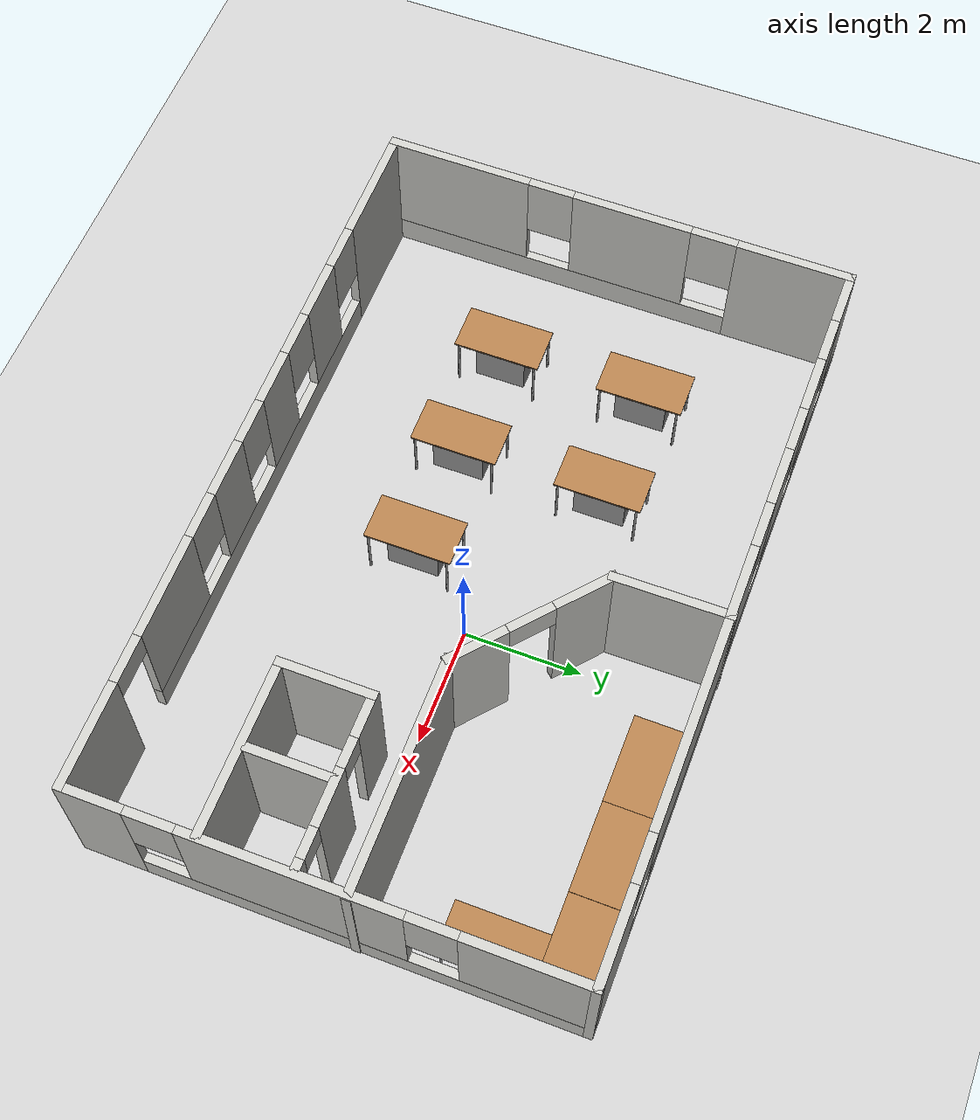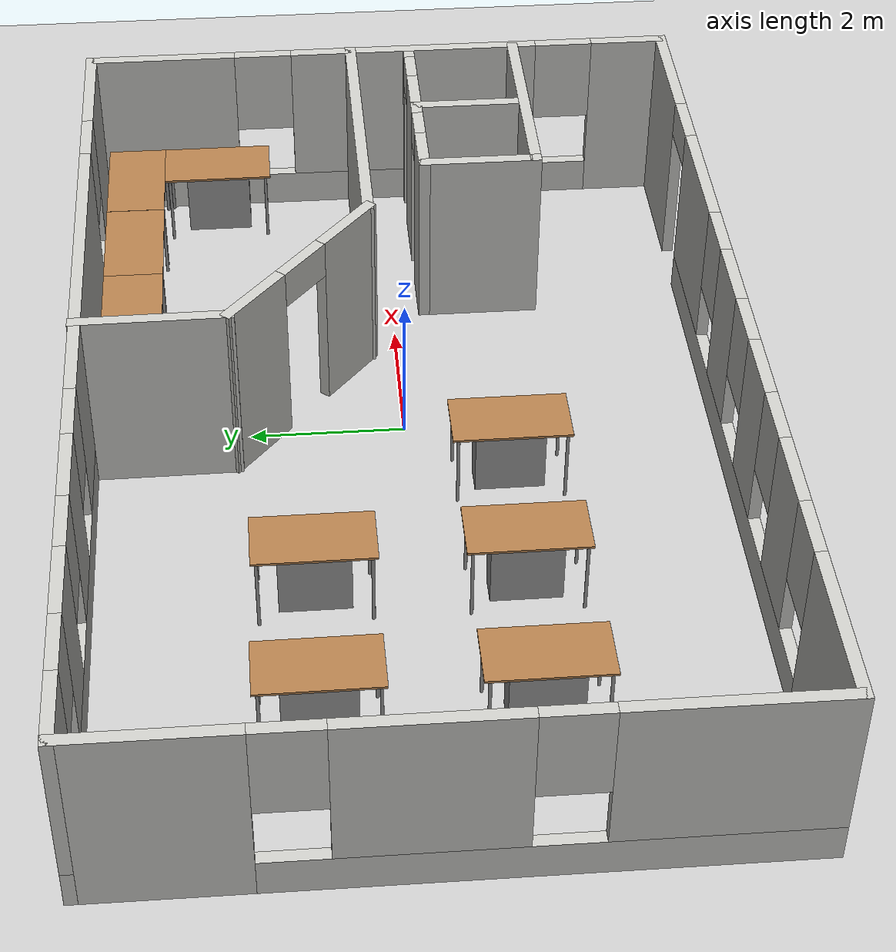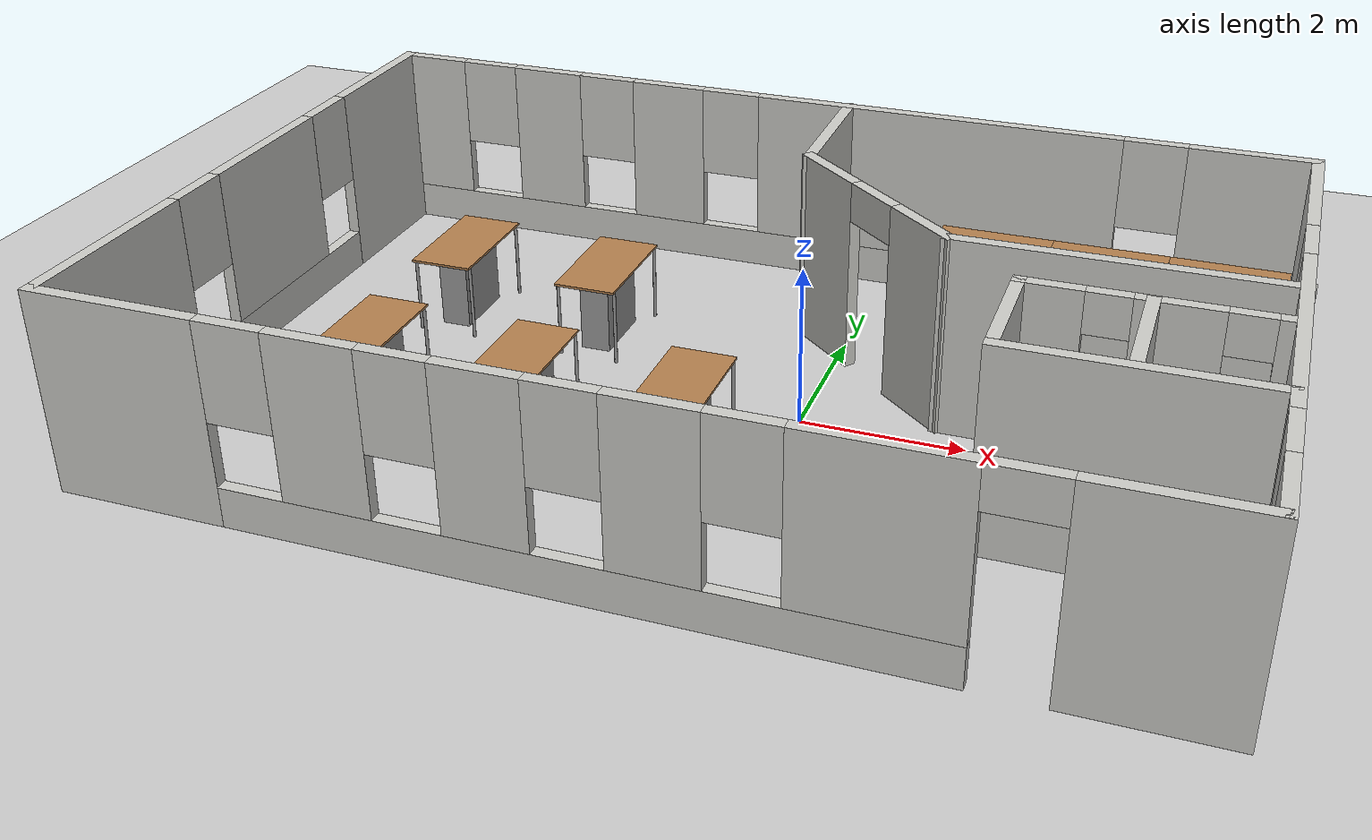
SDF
<sdf version="1.6">
 <world name="default">
  <light name="sun" type="directional">
   <pose>0 0 10 0 -0 0</pose>
   <diffuse>0.8 0.8 0.8 1</diffuse>
   <specular>0.2 0.2 0.2 1</specular>
   <attenuation>
    <range>1000</range>
    <constant>0.9</constant>
    <linear>0.01</linear>
    <quadratic>0.001</quadratic>
   </attenuation>
   <direction>-0.5 0.1 -0.9</direction>
  </light>
  <model name="ground_plane">
   <static>1</static>
   <link name="link">
    <collision name="collision">
     <geometry><plane><normal>0 0 1</normal><size>100 100</size></plane></geometry>
     <surface><friction><ode><mu>100</mu><mu2>50</mu2></ode></friction></surface>
    </collision>
    <visual name="visual">
     <cast_shadows>0</cast_shadows>
     <geometry><plane><normal>0 0 1</normal><size>100 100</size></plane></geometry>
     <material>
      <script><uri>file://media/materials/scripts/gazebo.material</uri><name>Gazebo/Grey</name></script>
     </material>
    </visual>
   </link>
  </model>
  <physics name="default_physics" default="0" type="ode">
   <real_time_update_rate>10000</real_time_update_rate>
   <max_step_size>0.001</max_step_size>
   <real_time_factor>1</real_time_factor>
   <ode>
    <solver>
     <type>quick</type>
     <iters>150</iters>
     <precon_iters>0</precon_iters>
     <sor>1.4</sor>
     <use_dynamic_moi_rescaling>1</use_dynamic_moi_rescaling>
    </solver>
    <constraints>
     <cfm>1e-05</cfm>
     <erp>0.2</erp>
     <contact_max_correcting_vel>2000</contact_max_correcting_vel>
     <contact_surface_layer>0.01</contact_surface_layer>
    </constraints>
   </ode>
  </physics>
  <gravity>0 0 -9.8</gravity>
  <magnetic_field>6e-06 2.3e-05 -4.2e-05</magnetic_field>
  <atmosphere type="adiabatic"/>
  <scene><ambient>0.4 0.4 0.4 1</ambient><background>0.7 0.7 0.7 1</background><shadows>1</shadows></scene>
  <spherical_coordinates>
   <surface_model>EARTH_WGS84</surface_model>
   <latitude_deg>0</latitude_deg>
   <longitude_deg>0</longitude_deg>
   <elevation>0</elevation>
   <heading_deg>0</heading_deg>
  </spherical_coordinates>
  <model name="restaurant">
   <pose>-0.910578 -0.005951 0 0 -0 0</pose>
   <link name="Wall_0">
    <pose>-0.00791 4.04129 0 0 -0 3.14159</pose>
    <visual name="Wall_0_Visual_0">
     <pose>-5.56163 0 1.25 0 -0 0</pose>
     <geometry><box><size>1.62673 0.15 2.5</size></box></geometry>
     <material>
      <script><uri>file://media/materials/scripts/gazebo.material</uri><name>Gazebo/CeilingTiled</name></script>
      <ambient>1 1 1 1</ambient>
     </material>
     <meta><layer>0</layer></meta>
    </visual>
    <collision name="Wall_0_Collision_0">
     <geometry><box><size>1.62673 0.15 2.5</size></box></geometry>
     <pose>-5.56163 0 1.25 0 -0 0</pose>
    </collision>
    <visual name="Wall_0_Visual_1">
     <pose>0.813365 0 0.25 0 -0 0</pose>
     <geometry><box><size>11.1233 0.15 0.5</size></box></geometry>
     <material>
      <script><uri>file://media/materials/scripts/gazebo.material</uri><name>Gazebo/CeilingTiled</name></script>
      <ambient>1 1 1 1</ambient>
     </material>
     <meta><layer>0</layer></meta>
    </visual>
    <collision name="Wall_0_Collision_1">
     <geometry><box><size>11.1233 0.15 0.5</size></box></geometry>
     <pose>0.813365 0 0.25 0 -0 0</pose>
    </collision>
    <visual name="Wall_0_Visual_2">
     <pose>-1.50614 0 1.5 0 -0 0</pose>
     <geometry><box><size>4.88427 0.15 2</size></box></geometry>
     <material>
      <script><uri>file://media/materials/scripts/gazebo.material</uri><name>Gazebo/CeilingTiled</name></script>
      <ambient>1 1 1 1</ambient>
     </material>
     <meta><layer>0</layer></meta>
    </visual>
    <collision name="Wall_0_Collision_2">
     <geometry><box><size>4.88427 0.15 2</size></box></geometry>
     <pose>-1.50614 0 1.5 0 -0 0</pose>
    </collision>
    <visual name="Wall_0_Visual_3">
     <pose>2.25423 0 1.5 0 -0 0</pose>
     <geometry><box><size>1.03646 0.15 2</size></box></geometry>
     <material>
      <script><uri>file://media/materials/scripts/gazebo.material</uri><name>Gazebo/CeilingTiled</name></script>
      <ambient>1 1 1 1</ambient>
     </material>
     <meta><layer>0</layer></meta>
    </visual>
    <collision name="Wall_0_Collision_3">
     <geometry><box><size>1.03646 0.15 2</size></box></geometry>
     <pose>2.25423 0 1.5 0 -0 0</pose>
    </collision>
    <visual name="Wall_0_Visual_4">
     <pose>4.07319 0 1.5 0 -0 0</pose>
     <geometry><box><size>1.00148 0.15 2</size></box></geometry>
     <material>
      <script><uri>file://media/materials/scripts/gazebo.material</uri><name>Gazebo/CeilingTiled</name></script>
      <ambient>1 1 1 1</ambient>
     </material>
     <meta><layer>0</layer></meta>
    </visual>
    <collision name="Wall_0_Collision_4">
     <geometry><box><size>1.00148 0.15 2</size></box></geometry>
     <pose>4.07319 0 1.5 0 -0 0</pose>
    </collision>
    <visual name="Wall_0_Visual_5">
     <pose>5.87447 0 1.5 0 -0 0</pose>
     <geometry><box><size>1.00107 0.15 2</size></box></geometry>
     <material>
      <script><uri>file://media/materials/scripts/gazebo.material</uri><name>Gazebo/CeilingTiled</name></script>
      <ambient>1 1 1 1</ambient>
     </material>
     <meta><layer>0</layer></meta>
    </visual>
    <collision name="Wall_0_Collision_5">
     <geometry><box><size>1.00107 0.15 2</size></box></geometry>
     <pose>5.87447 0 1.5 0 -0 0</pose>
    </collision>
    <visual name="Wall_0_Visual_6">
     <pose>-4.34827 0 1.9 0 -0 0</pose>
     <geometry><box><size>0.8 0.15 1.2</size></box></geometry>
     <material>
      <script><uri>file://media/materials/scripts/gazebo.material</uri><name>Gazebo/CeilingTiled</name></script>
      <ambient>1 1 1 1</ambient>
     </material>
     <meta><layer>0</layer></meta>
    </visual>
    <collision name="Wall_0_Collision_6">
     <geometry><box><size>0.8 0.15 1.2</size></box></geometry>
     <pose>-4.34827 0 1.9 0 -0 0</pose>
    </collision>
    <visual name="Wall_0_Visual_7">
     <pose>1.336 0 1.9 0 -0 0</pose>
     <geometry><box><size>0.8 0.15 1.2</size></box></geometry>
     <material>
      <script><uri>file://media/materials/scripts/gazebo.material</uri><name>Gazebo/CeilingTiled</name></script>
      <ambient>1 1 1 1</ambient>
     </material>
     <meta><layer>0</layer></meta>
    </visual>
    <collision name="Wall_0_Collision_7">
     <geometry><box><size>0.8 0.15 1.2</size></box></geometry>
     <pose>1.336 0 1.9 0 -0 0</pose>
    </collision>
    <visual name="Wall_0_Visual_8">
     <pose>3.17246 0 1.9 0 -0 0</pose>
     <geometry><box><size>0.8 0.15 1.2</size></box></geometry>
     <material>
      <script><uri>file://media/materials/scripts/gazebo.material</uri><name>Gazebo/CeilingTiled</name></script>
      <ambient>1 1 1 1</ambient>
     </material>
     <meta><layer>0</layer></meta>
    </visual>
    <collision name="Wall_0_Collision_8">
     <geometry><box><size>0.8 0.15 1.2</size></box></geometry>
     <pose>3.17246 0 1.9 0 -0 0</pose>
    </collision>
    <visual name="Wall_0_Visual_9">
     <pose>4.97393 0 1.9 0 -0 0</pose>
     <geometry><box><size>0.8 0.15 1.2</size></box></geometry>
     <material>
      <script><uri>file://media/materials/scripts/gazebo.material</uri><name>Gazebo/CeilingTiled</name></script>
      <ambient>1 1 1 1</ambient>
     </material>
     <meta><layer>0</layer></meta>
    </visual>
    <collision name="Wall_0_Collision_9">
     <geometry><box><size>0.8 0.15 1.2</size></box></geometry>
     <pose>4.97393 0 1.9 0 -0 0</pose>
    </collision>
   </link>
   <link name="Wall_1">
    <pose>-6.30791 -0.008707 0 0 0 -1.5708</pose>
    <visual name="Wall_1_Visual_0">
     <pose>-3.11766 0 1.25 0 -0 0</pose>
     <geometry><box><size>2.01468 0.15 2.5</size></box></geometry>
     <material>
      <script><uri>file://media/materials/scripts/gazebo.material</uri><name>Gazebo/CeilingTiled</name></script>
      <ambient>1 1 1 1</ambient>
     </material>
     <meta><layer>0</layer></meta>
    </visual>
    <collision name="Wall_1_Collision_0">
     <geometry><box><size>2.01468 0.15 2.5</size></box></geometry>
     <pose>-3.11766 0 1.25 0 -0 0</pose>
    </collision>
    <visual name="Wall_1_Visual_1">
     <pose>1.00734 0 0.25 0 -0 0</pose>
     <geometry><box><size>6.23532 0.15 0.5</size></box></geometry>
     <material>
      <script><uri>file://media/materials/scripts/gazebo.material</uri><name>Gazebo/CeilingTiled</name></script>
      <ambient>1 1 1 1</ambient>
     </material>
     <meta><layer>0</layer></meta>
    </visual>
    <collision name="Wall_1_Collision_1">
     <geometry><box><size>6.23532 0.15 0.5</size></box></geometry>
     <pose>1.00734 0 0.25 0 -0 0</pose>
    </collision>
    <visual name="Wall_1_Visual_2">
     <pose>-0.267389 0 1.5 0 -0 0</pose>
     <geometry><box><size>2.08586 0.15 2</size></box></geometry>
     <material>
      <script><uri>file://media/materials/scripts/gazebo.material</uri><name>Gazebo/CeilingTiled</name></script>
      <ambient>1 1 1 1</ambient>
     </material>
     <meta><layer>0</layer></meta>
    </visual>
    <collision name="Wall_1_Collision_2">
     <geometry><box><size>2.08586 0.15 2</size></box></geometry>
     <pose>-0.267389 0 1.5 0 -0 0</pose>
    </collision>
    <visual name="Wall_1_Visual_3">
     <pose>2.85027 0 1.5 0 -0 0</pose>
     <geometry><box><size>2.54946 0.15 2</size></box></geometry>
     <material>
      <script><uri>file://media/materials/scripts/gazebo.material</uri><name>Gazebo/CeilingTiled</name></script>
      <ambient>1 1 1 1</ambient>
     </material>
     <meta><layer>0</layer></meta>
    </visual>
    <collision name="Wall_1_Collision_3">
     <geometry><box><size>2.54946 0.15 2</size></box></geometry>
     <pose>2.85027 0 1.5 0 -0 0</pose>
    </collision>
    <visual name="Wall_1_Visual_4">
     <pose>-1.71032 0 1.9 0 -0 0</pose>
     <geometry><box><size>0.8 0.15 1.2</size></box></geometry>
     <material>
      <script><uri>file://media/materials/scripts/gazebo.material</uri><name>Gazebo/CeilingTiled</name></script>
      <ambient>1 1 1 1</ambient>
     </material>
     <meta><layer>0</layer></meta>
    </visual>
    <collision name="Wall_1_Collision_4">
     <geometry><box><size>0.8 0.15 1.2</size></box></geometry>
     <pose>-1.71032 0 1.9 0 -0 0</pose>
    </collision>
    <visual name="Wall_1_Visual_5">
     <pose>1.17554 0 1.9 0 -0 0</pose>
     <geometry><box><size>0.8 0.15 1.2</size></box></geometry>
     <material>
      <script><uri>file://media/materials/scripts/gazebo.material</uri><name>Gazebo/CeilingTiled</name></script>
      <ambient>1 1 1 1</ambient>
     </material>
     <meta><layer>0</layer></meta>
    </visual>
    <collision name="Wall_1_Collision_5">
     <geometry><box><size>0.8 0.15 1.2</size></box></geometry>
     <pose>1.17554 0 1.9 0 -0 0</pose>
    </collision>
   </link>
   <link name="Wall_12">
    <collision name="Wall_12_Collision">
     <geometry><box><size>3 0.15 2.5</size></box></geometry>
     <pose>0 0 1.25 0 -0 0</pose>
    </collision>
    <visual name="Wall_12_Visual">
     <pose>0 0 1.25 0 -0 0</pose>
     <geometry><box><size>3 0.15 2.5</size></box></geometry>
     <material>
      <script><uri>file://media/materials/scripts/gazebo.material</uri><name>Gazebo/CeilingTiled</name></script>
      <ambient>1 1 1 1</ambient>
     </material>
     <meta><layer>0</layer></meta>
    </visual>
    <pose>4.83059 -1.92356 0 0 -0 3.14159</pose>
   </link>
   <link name="Wall_15">
    <pose>4.83059 -0.436903 0 0 -0 3.14159</pose>
    <visual name="Wall_15_Visual_0">
     <pose>-1.36407 0 1.25 0 -0 0</pose>
     <geometry><box><size>0.271862 0.15 2.5</size></box></geometry>
     <material>
      <script><uri>file://media/materials/scripts/gazebo.material</uri><name>Gazebo/CeilingTiled</name></script>
      <ambient>1 1 1 1</ambient>
     </material>
     <meta><layer>0</layer></meta>
    </visual>
    <collision name="Wall_15_Collision_0">
     <geometry><box><size>0.271862 0.15 2.5</size></box></geometry>
     <pose>-1.36407 0 1.25 0 -0 0</pose>
    </collision>
    <visual name="Wall_15_Visual_1">
     <pose>-0.253638 0 1.25 0 -0 0</pose>
     <geometry><box><size>0.949 0.15 2.5</size></box></geometry>
     <material>
      <script><uri>file://media/materials/scripts/gazebo.material</uri><name>Gazebo/CeilingTiled</name></script>
      <ambient>1 1 1 1</ambient>
     </material>
     <meta><layer>0</layer></meta>
    </visual>
    <collision name="Wall_15_Collision_1">
     <geometry><box><size>0.949 0.15 2.5</size></box></geometry>
     <pose>-0.253638 0 1.25 0 -0 0</pose>
    </collision>
    <visual name="Wall_15_Visual_2">
     <pose>1.11043 0 1.25 0 -0 0</pose>
     <geometry><box><size>0.779138 0.15 2.5</size></box></geometry>
     <material>
      <script><uri>file://media/materials/scripts/gazebo.material</uri><name>Gazebo/CeilingTiled</name></script>
      <ambient>1 1 1 1</ambient>
     </material>
     <meta><layer>0</layer></meta>
    </visual>
    <collision name="Wall_15_Collision_2">
     <geometry><box><size>0.779138 0.15 2.5</size></box></geometry>
     <pose>1.11043 0 1.25 0 -0 0</pose>
    </collision>
    <visual name="Wall_15_Visual_3">
     <pose>-0.978138 0 2.25 0 -0 0</pose>
     <geometry><box><size>0.5 0.15 0.5</size></box></geometry>
     <material>
      <script><uri>file://media/materials/scripts/gazebo.material</uri><name>Gazebo/CeilingTiled</name></script>
      <ambient>1 1 1 1</ambient>
     </material>
     <meta><layer>0</layer></meta>
    </visual>
    <collision name="Wall_15_Collision_3">
     <geometry><box><size>0.5 0.15 0.5</size></box></geometry>
     <pose>-0.978138 0 2.25 0 -0 0</pose>
    </collision>
    <visual name="Wall_15_Visual_4">
     <pose>0.470862 0 2.25 0 -0 0</pose>
     <geometry><box><size>0.5 0.15 0.5</size></box></geometry>
     <material>
      <script><uri>file://media/materials/scripts/gazebo.material</uri><name>Gazebo/CeilingTiled</name></script>
      <ambient>1 1 1 1</ambient>
     </material>
     <meta><layer>0</layer></meta>
    </visual>
    <collision name="Wall_15_Collision_4">
     <geometry><box><size>0.5 0.15 0.5</size></box></geometry>
     <pose>0.470862 0 2.25 0 -0 0</pose>
    </collision>
   </link>
   <link name="Wall_16">
    <collision name="Wall_16_Collision">
     <geometry><box><size>1.63665 0.15 2.5</size></box></geometry>
     <pose>0 0 1.25 0 -0 0</pose>
    </collision>
    <visual name="Wall_16_Visual">
     <pose>0 0 1.25 0 -0 0</pose>
     <geometry><box><size>1.63665 0.15 2.5</size></box></geometry>
     <material>
      <script><uri>file://media/materials/scripts/gazebo.material</uri><name>Gazebo/CeilingTiled</name></script>
      <ambient>1 1 1 1</ambient>
     </material>
     <meta><layer>0</layer></meta>
    </visual>
    <pose>3.40559 -1.18023 0 0 0 -1.5708</pose>
   </link>
   <link name="Wall_18">
    <collision name="Wall_18_Collision">
     <geometry><box><size>1.5 0.15 2.5</size></box></geometry>
     <pose>0 0 1.25 0 -0 0</pose>
    </collision>
    <visual name="Wall_18_Visual">
     <pose>0 0 1.25 0 -0 0</pose>
     <geometry><box><size>1.5 0.15 2.5</size></box></geometry>
     <material>
      <script><uri>file://media/materials/scripts/gazebo.material</uri><name>Gazebo/CeilingTiled</name></script>
      <ambient>1 1 1 1</ambient>
     </material>
     <meta><layer>0</layer></meta>
    </visual>
    <pose>4.80391 -1.12939 0 0 0 -1.5708</pose>
   </link>
   <link name="Wall_2">
    <pose>-0.00791 -4.05871 0 0 -0 0</pose>
    <visual name="Wall_2_Visual_0">
     <pose>-5.32353 0 1.25 0 -0 0</pose>
     <geometry><box><size>2.10294 0.15 2.5</size></box></geometry>
     <material>
      <script><uri>file://media/materials/scripts/gazebo.material</uri><name>Gazebo/CeilingTiled</name></script>
      <ambient>1 1 1 1</ambient>
     </material>
     <meta><layer>0</layer></meta>
    </visual>
    <collision name="Wall_2_Collision_0">
     <geometry><box><size>2.10294 0.15 2.5</size></box></geometry>
     <pose>-5.32353 0 1.25 0 -0 0</pose>
    </collision>
    <visual name="Wall_2_Visual_1">
     <pose>5.47361 0 1.25 0 -0 0</pose>
     <geometry><box><size>1.80279 0.15 2.5</size></box></geometry>
     <material>
      <script><uri>file://media/materials/scripts/gazebo.material</uri><name>Gazebo/CeilingTiled</name></script>
      <ambient>1 1 1 1</ambient>
     </material>
     <meta><layer>0</layer></meta>
    </visual>
    <collision name="Wall_2_Collision_1">
     <geometry><box><size>1.80279 0.15 2.5</size></box></geometry>
     <pose>5.47361 0 1.25 0 -0 0</pose>
    </collision>
    <visual name="Wall_2_Visual_2">
     <pose>-0.249924 0 0.25 0 -0 0</pose>
     <geometry><box><size>8.04427 0.15 0.5</size></box></geometry>
     <material>
      <script><uri>file://media/materials/scripts/gazebo.material</uri><name>Gazebo/CeilingTiled</name></script>
      <ambient>1 1 1 1</ambient>
     </material>
     <meta><layer>0</layer></meta>
    </visual>
    <collision name="Wall_2_Collision_2">
     <geometry><box><size>8.04427 0.15 0.5</size></box></geometry>
     <pose>-0.249924 0 0.25 0 -0 0</pose>
    </collision>
    <visual name="Wall_2_Visual_3">
     <pose>-2.94509 0 1.5 0 -0 0</pose>
     <geometry><box><size>1.05395 0.15 2</size></box></geometry>
     <material>
      <script><uri>file://media/materials/scripts/gazebo.material</uri><name>Gazebo/CeilingTiled</name></script>
      <ambient>1 1 1 1</ambient>
     </material>
     <meta><layer>0</layer></meta>
    </visual>
    <collision name="Wall_2_Collision_3">
     <geometry><box><size>1.05395 0.15 2</size></box></geometry>
     <pose>-2.94509 0 1.5 0 -0 0</pose>
    </collision>
    <visual name="Wall_2_Visual_4">
     <pose>-1.12612 0 1.5 0 -0 0</pose>
     <geometry><box><size>0.983986 0.15 2</size></box></geometry>
     <material>
      <script><uri>file://media/materials/scripts/gazebo.material</uri><name>Gazebo/CeilingTiled</name></script>
      <ambient>1 1 1 1</ambient>
     </material>
     <meta><layer>0</layer></meta>
    </visual>
    <collision name="Wall_2_Collision_4">
     <geometry><box><size>0.983986 0.15 2</size></box></geometry>
     <pose>-1.12612 0 1.5 0 -0 0</pose>
    </collision>
    <visual name="Wall_2_Visual_5">
     <pose>0.675358 0 1.5 0 -0 0</pose>
     <geometry><box><size>1.01897 0.15 2</size></box></geometry>
     <material>
      <script><uri>file://media/materials/scripts/gazebo.material</uri><name>Gazebo/CeilingTiled</name></script>
      <ambient>1 1 1 1</ambient>
     </material>
     <meta><layer>0</layer></meta>
    </visual>
    <collision name="Wall_2_Collision_5">
     <geometry><box><size>1.01897 0.15 2</size></box></geometry>
     <pose>0.675358 0 1.5 0 -0 0</pose>
    </collision>
    <visual name="Wall_2_Visual_6">
     <pose>2.87853 0 1.5 0 -0 0</pose>
     <geometry><box><size>1.78737 0.15 2</size></box></geometry>
     <material>
      <script><uri>file://media/materials/scripts/gazebo.material</uri><name>Gazebo/CeilingTiled</name></script>
      <ambient>1 1 1 1</ambient>
     </material>
     <meta><layer>0</layer></meta>
    </visual>
    <collision name="Wall_2_Collision_6">
     <geometry><box><size>1.78737 0.15 2</size></box></geometry>
     <pose>2.87853 0 1.5 0 -0 0</pose>
    </collision>
    <visual name="Wall_2_Visual_7">
     <pose>-3.87206 0 1.9 0 -0 0</pose>
     <geometry><box><size>0.8 0.15 1.2</size></box></geometry>
     <material>
      <script><uri>file://media/materials/scripts/gazebo.material</uri><name>Gazebo/CeilingTiled</name></script>
      <ambient>1 1 1 1</ambient>
     </material>
     <meta><layer>0</layer></meta>
    </visual>
    <collision name="Wall_2_Collision_7">
     <geometry><box><size>0.8 0.15 1.2</size></box></geometry>
     <pose>-3.87206 0 1.9 0 -0 0</pose>
    </collision>
    <visual name="Wall_2_Visual_8">
     <pose>-2.01811 0 1.9 0 -0 0</pose>
     <geometry><box><size>0.8 0.15 1.2</size></box></geometry>
     <material>
      <script><uri>file://media/materials/scripts/gazebo.material</uri><name>Gazebo/CeilingTiled</name></script>
      <ambient>1 1 1 1</ambient>
     </material>
     <meta><layer>0</layer></meta>
    </visual>
    <collision name="Wall_2_Collision_8">
     <geometry><box><size>0.8 0.15 1.2</size></box></geometry>
     <pose>-2.01811 0 1.9 0 -0 0</pose>
    </collision>
    <visual name="Wall_2_Visual_9">
     <pose>-0.234126 0 1.9 0 -0 0</pose>
     <geometry><box><size>0.8 0.15 1.2</size></box></geometry>
     <material>
      <script><uri>file://media/materials/scripts/gazebo.material</uri><name>Gazebo/CeilingTiled</name></script>
      <ambient>1 1 1 1</ambient>
     </material>
     <meta><layer>0</layer></meta>
    </visual>
    <collision name="Wall_2_Collision_9">
     <geometry><box><size>0.8 0.15 1.2</size></box></geometry>
     <pose>-0.234126 0 1.9 0 -0 0</pose>
    </collision>
    <visual name="Wall_2_Visual_10">
     <pose>1.58484 0 1.9 0 -0 0</pose>
     <geometry><box><size>0.8 0.15 1.2</size></box></geometry>
     <material>
      <script><uri>file://media/materials/scripts/gazebo.material</uri><name>Gazebo/CeilingTiled</name></script>
      <ambient>1 1 1 1</ambient>
     </material>
     <meta><layer>0</layer></meta>
    </visual>
    <collision name="Wall_2_Collision_10">
     <geometry><box><size>0.8 0.15 1.2</size></box></geometry>
     <pose>1.58484 0 1.9 0 -0 0</pose>
    </collision>
    <visual name="Wall_2_Visual_11">
     <pose>4.17221 0 2.25 0 -0 0</pose>
     <geometry><box><size>0.8 0.15 0.5</size></box></geometry>
     <material>
      <script><uri>file://media/materials/scripts/gazebo.material</uri><name>Gazebo/CeilingTiled</name></script>
      <ambient>1 1 1 1</ambient>
     </material>
     <meta><layer>0</layer></meta>
    </visual>
    <collision name="Wall_2_Collision_11">
     <geometry><box><size>0.8 0.15 0.5</size></box></geometry>
     <pose>4.17221 0 2.25 0 -0 0</pose>
    </collision>
   </link>
   <link name="Wall_3">
    <pose>6.29209 -0.008707 0 0 -0 1.5708</pose>
    <visual name="Wall_3_Visual_0">
     <pose>-3.58485 0 1.25 0 -0 0</pose>
     <geometry><box><size>1.08029 0.15 2.5</size></box></geometry>
     <material>
      <script><uri>file://media/materials/scripts/gazebo.material</uri><name>Gazebo/CeilingTiled</name></script>
      <ambient>1 1 1 1</ambient>
     </material>
     <meta><layer>0</layer></meta>
    </visual>
    <collision name="Wall_3_Collision_0">
     <geometry><box><size>1.08029 0.15 2.5</size></box></geometry>
     <pose>-3.58485 0 1.25 0 -0 0</pose>
    </collision>
    <visual name="Wall_3_Visual_1">
     <pose>0.540147 0 0.25 0 -0 0</pose>
     <geometry><box><size>7.16971 0.15 0.5</size></box></geometry>
     <material>
      <script><uri>file://media/materials/scripts/gazebo.material</uri><name>Gazebo/CeilingTiled</name></script>
      <ambient>1 1 1 1</ambient>
     </material>
     <meta><layer>0</layer></meta>
    </visual>
    <collision name="Wall_3_Collision_1">
     <geometry><box><size>7.16971 0.15 0.5</size></box></geometry>
     <pose>0.540147 0 0.25 0 -0 0</pose>
    </collision>
    <visual name="Wall_3_Visual_2">
     <pose>-0.502174 0 1.5 0 -0 0</pose>
     <geometry><box><size>3.48507 0.15 2</size></box></geometry>
     <material>
      <script><uri>file://media/materials/scripts/gazebo.material</uri><name>Gazebo/CeilingTiled</name></script>
      <ambient>1 1 1 1</ambient>
     </material>
     <meta><layer>0</layer></meta>
    </visual>
    <collision name="Wall_3_Collision_2">
     <geometry><box><size>3.48507 0.15 2</size></box></geometry>
     <pose>-0.502174 0 1.5 0 -0 0</pose>
    </collision>
    <visual name="Wall_3_Visual_3">
     <pose>3.08268 0 1.5 0 -0 0</pose>
     <geometry><box><size>2.08464 0.15 2</size></box></geometry>
     <material>
      <script><uri>file://media/materials/scripts/gazebo.material</uri><name>Gazebo/CeilingTiled</name></script>
      <ambient>1 1 1 1</ambient>
     </material>
     <meta><layer>0</layer></meta>
    </visual>
    <collision name="Wall_3_Collision_3">
     <geometry><box><size>2.08464 0.15 2</size></box></geometry>
     <pose>3.08268 0 1.5 0 -0 0</pose>
    </collision>
    <visual name="Wall_3_Visual_4">
     <pose>-2.64471 0 1.9 0 -0 0</pose>
     <geometry><box><size>0.8 0.15 1.2</size></box></geometry>
     <material>
      <script><uri>file://media/materials/scripts/gazebo.material</uri><name>Gazebo/CeilingTiled</name></script>
      <ambient>1 1 1 1</ambient>
     </material>
     <meta><layer>0</layer></meta>
    </visual>
    <collision name="Wall_3_Collision_4">
     <geometry><box><size>0.8 0.15 1.2</size></box></geometry>
     <pose>-2.64471 0 1.9 0 -0 0</pose>
    </collision>
    <visual name="Wall_3_Visual_5">
     <pose>1.64036 0 1.9 0 -0 0</pose>
     <geometry><box><size>0.8 0.15 1.2</size></box></geometry>
     <material>
      <script><uri>file://media/materials/scripts/gazebo.material</uri><name>Gazebo/CeilingTiled</name></script>
      <ambient>1 1 1 1</ambient>
     </material>
     <meta><layer>0</layer></meta>
    </visual>
    <collision name="Wall_3_Collision_5">
     <geometry><box><size>0.8 0.15 1.2</size></box></geometry>
     <pose>1.64036 0 1.9 0 -0 0</pose>
    </collision>
   </link>
   <link name="Wall_5">
    <collision name="Wall_5_Collision">
     <geometry><box><size>2.01717 0.15 2.5</size></box></geometry>
     <pose>0 0 1.25 0 -0 0</pose>
    </collision>
    <visual name="Wall_5_Visual">
     <pose>0 0 1.25 0 -0 0</pose>
     <geometry><box><size>2.01717 0.15 2.5</size></box></geometry>
     <material>
      <script><uri>file://media/materials/scripts/gazebo.material</uri><name>Gazebo/CeilingTiled</name></script>
      <ambient>1 1 1 1</ambient>
     </material>
     <meta><layer>0</layer></meta>
    </visual>
    <pose>0.317273 3.1245 0 0 0 -1.5619</pose>
   </link>
   <link name="Wall_7">
    <collision name="Wall_7_Collision">
     <geometry><box><size>3.98304 0.15 2.5</size></box></geometry>
     <pose>0 0 1.25 0 -0 0</pose>
    </collision>
    <visual name="Wall_7_Visual">
     <pose>0 0 1.25 0 -0 0</pose>
     <geometry><box><size>3.98304 0.15 2.5</size></box></geometry>
     <material>
      <script><uri>file://media/materials/scripts/gazebo.material</uri><name>Gazebo/CeilingTiled</name></script>
      <ambient>1 1 1 1</ambient>
     </material>
     <meta><layer>0</layer></meta>
    </visual>
    <pose>4.39108 0.376451 0 0 0 -3.13716</pose>
   </link>
   <link name="Wall_9">
    <pose>1.40008 1.27945 0 0 0 -0.703507</pose>
    <visual name="Wall_9_Visual_0">
     <pose>-0.939222 0 1.25 0 -0 0</pose>
     <geometry><box><size>1.08963 0.15 2.5</size></box></geometry>
     <material>
      <script><uri>file://media/materials/scripts/gazebo.material</uri><name>Gazebo/CeilingTiled</name></script>
      <ambient>1 1 1 1</ambient>
     </material>
     <meta><layer>0</layer></meta>
    </visual>
    <collision name="Wall_9_Collision_0">
     <geometry><box><size>1.08963 0.15 2.5</size></box></geometry>
     <pose>-0.939222 0 1.25 0 -0 0</pose>
    </collision>
    <visual name="Wall_9_Visual_1">
     <pose>0.944814 0 1.25 0 -0 0</pose>
     <geometry><box><size>1.07844 0.15 2.5</size></box></geometry>
     <material>
      <script><uri>file://media/materials/scripts/gazebo.material</uri><name>Gazebo/CeilingTiled</name></script>
      <ambient>1 1 1 1</ambient>
     </material>
     <meta><layer>0</layer></meta>
    </visual>
    <collision name="Wall_9_Collision_1">
     <geometry><box><size>1.07844 0.15 2.5</size></box></geometry>
     <pose>0.944814 0 1.25 0 -0 0</pose>
    </collision>
    <visual name="Wall_9_Visual_2">
     <pose>0.005593 0 2.25 0 -0 0</pose>
     <geometry><box><size>0.8 0.15 0.5</size></box></geometry>
     <material>
      <script><uri>file://media/materials/scripts/gazebo.material</uri><name>Gazebo/CeilingTiled</name></script>
      <ambient>1 1 1 1</ambient>
     </material>
     <meta><layer>0</layer></meta>
    </visual>
    <collision name="Wall_9_Collision_2">
     <geometry><box><size>0.8 0.15 0.5</size></box></geometry>
     <pose>0.005593 0 2.25 0 -0 0</pose>
    </collision>
   </link>
   <static>1</static>
  </model>
  <model name="table-solid">
   <link name="link">
    <visual name="visual1">
     <pose>0 0 1 0 -0 0</pose>
     <geometry><box><size>1.5 0.8 0.03</size></box></geometry>
     <material>
      <script><uri>file://media/materials/scripts/gazebo.material</uri><name>Gazebo/Wood</name></script>
      <shader type="pixel"/>
      <ambient>1 1 1 1</ambient>
      <diffuse>1 1 1 1</diffuse>
      <specular>0.2 0.2 0.2 1</specular>
      <emissive>0 0 0 1</emissive>
     </material>
    </visual>
    <visual name="front_left_leg">
     <pose>0.68 0.38 0.5 0 -0 0</pose>
     <geometry><cylinder><radius>0.02</radius><length>1</length></cylinder></geometry>
     <material>
      <script><uri>file://media/materials/scripts/gazebo.material</uri><name>Gazebo/Grey</name></script>
      <shader type="pixel"/>
      <ambient>0.3 0.3 0.3 1</ambient>
      <diffuse>0.7 0.7 0.7 1</diffuse>
      <specular>0.01 0.01 0.01 1</specular>
      <emissive>0 0 0 1</emissive>
     </material>
    </visual>
    <visual name="front_right_leg">
     <pose>0.68 -0.38 0.5 0 -0 0</pose>
     <geometry><cylinder><radius>0.02</radius><length>1</length></cylinder></geometry>
     <material>
      <script><uri>file://media/materials/scripts/gazebo.material</uri><name>Gazebo/Grey</name></script>
      <shader type="pixel"/>
      <ambient>0.3 0.3 0.3 1</ambient>
      <diffuse>0.7 0.7 0.7 1</diffuse>
      <specular>0.01 0.01 0.01 1</specular>
      <emissive>0 0 0 1</emissive>
     </material>
    </visual>
    <visual name="back_right_leg">
     <pose>-0.68 -0.38 0.5 0 -0 0</pose>
     <geometry><cylinder><radius>0.02</radius><length>1</length></cylinder></geometry>
     <material>
      <script><uri>file://media/materials/scripts/gazebo.material</uri><name>Gazebo/Grey</name></script>
      <shader type="pixel"/>
      <ambient>0.3 0.3 0.3 1</ambient>
      <diffuse>0.7 0.7 0.7 1</diffuse>
      <specular>0.01 0.01 0.01 1</specular>
      <emissive>0 0 0 1</emissive>
     </material>
    </visual>
    <visual name="back_left_leg">
     <pose>-0.68 0.38 0.5 0 -0 0</pose>
     <geometry><cylinder><radius>0.02</radius><length>1</length></cylinder></geometry>
     <material>
      <script><uri>file://media/materials/scripts/gazebo.material</uri><name>Gazebo/Grey</name></script>
      <shader type="pixel"/>
      <ambient>0.3 0.3 0.3 1</ambient>
      <diffuse>0.7 0.7 0.7 1</diffuse>
      <specular>0.01 0.01 0.01 1</specular>
      <emissive>0 0 0 1</emissive>
     </material>
    </visual>
    <collision name="surface">
     <pose>0 0 1 0 -0 0</pose>
     <geometry><box><size>1.5 0.8 0.03</size></box></geometry>
     <surface>
      <friction>
       <ode><mu>0.6</mu><mu2>0.6</mu2><fdir1>0 0 0</fdir1><slip1>0</slip1><slip2>0</slip2></ode>
       <torsional>
        <coefficient>1</coefficient>
        <patch_radius>0</patch_radius>
        <surface_radius>0</surface_radius>
        <use_patch_radius>1</use_patch_radius>
        <ode><slip>0</slip></ode>
       </torsional>
      </friction>
      <bounce><restitution_coefficient>0</restitution_coefficient><threshold>1e+06</threshold></bounce>
      <contact>
       <collide_without_contact>0</collide_without_contact>
       <collide_without_contact_bitmask>1</collide_without_contact_bitmask>
       <collide_bitmask>1</collide_bitmask>
       <ode>
        <soft_cfm>0</soft_cfm>
        <soft_erp>0.2</soft_erp>
        <kp>1e+13</kp>
        <kd>1</kd>
        <max_vel>0.01</max_vel>
        <min_depth>0</min_depth>
       </ode>
       <bullet>
        <split_impulse>1</split_impulse>
        <split_impulse_penetration_threshold>-0.01</split_impulse_penetration_threshold>
        <soft_cfm>0</soft_cfm>
        <soft_erp>0.2</soft_erp>
        <kp>1e+13</kp>
        <kd>1</kd>
       </bullet>
      </contact>
     </surface>
    </collision>
    <collision name="front_left_leg">
     <pose>0.68 0.38 0.5 0 -0 0</pose>
     <geometry><cylinder><radius>0.02</radius><length>1</length></cylinder></geometry>
     <surface>
      <friction>
       <ode><mu>1</mu><mu2>1</mu2><fdir1>0 0 0</fdir1><slip1>0</slip1><slip2>0</slip2></ode>
       <torsional>
        <coefficient>1</coefficient>
        <patch_radius>0</patch_radius>
        <surface_radius>0</surface_radius>
        <use_patch_radius>1</use_patch_radius>
        <ode><slip>0</slip></ode>
       </torsional>
      </friction>
      <bounce><restitution_coefficient>0</restitution_coefficient><threshold>1e+06</threshold></bounce>
      <contact>
       <collide_without_contact>0</collide_without_contact>
       <collide_without_contact_bitmask>1</collide_without_contact_bitmask>
       <collide_bitmask>1</collide_bitmask>
       <ode>
        <soft_cfm>0</soft_cfm>
        <soft_erp>0.2</soft_erp>
        <kp>1e+13</kp>
        <kd>1</kd>
        <max_vel>0.01</max_vel>
        <min_depth>0</min_depth>
       </ode>
       <bullet>
        <split_impulse>1</split_impulse>
        <split_impulse_penetration_threshold>-0.01</split_impulse_penetration_threshold>
        <soft_cfm>0</soft_cfm>
        <soft_erp>0.2</soft_erp>
        <kp>1e+13</kp>
        <kd>1</kd>
       </bullet>
      </contact>
     </surface>
    </collision>
    <collision name="front_right_leg">
     <pose>0.68 -0.38 0.5 0 -0 0</pose>
     <geometry><cylinder><radius>0.02</radius><length>1</length></cylinder></geometry>
     <surface>
      <friction>
       <ode><mu>1</mu><mu2>1</mu2><fdir1>0 0 0</fdir1><slip1>0</slip1><slip2>0</slip2></ode>
       <torsional>
        <coefficient>1</coefficient>
        <patch_radius>0</patch_radius>
        <surface_radius>0</surface_radius>
        <use_patch_radius>1</use_patch_radius>
        <ode><slip>0</slip></ode>
       </torsional>
      </friction>
      <bounce><restitution_coefficient>0</restitution_coefficient><threshold>1e+06</threshold></bounce>
      <contact>
       <collide_without_contact>0</collide_without_contact>
       <collide_without_contact_bitmask>1</collide_without_contact_bitmask>
       <collide_bitmask>1</collide_bitmask>
       <ode>
        <soft_cfm>0</soft_cfm>
        <soft_erp>0.2</soft_erp>
        <kp>1e+13</kp>
        <kd>1</kd>
        <max_vel>0.01</max_vel>
        <min_depth>0</min_depth>
       </ode>
       <bullet>
        <split_impulse>1</split_impulse>
        <split_impulse_penetration_threshold>-0.01</split_impulse_penetration_threshold>
        <soft_cfm>0</soft_cfm>
        <soft_erp>0.2</soft_erp>
        <kp>1e+13</kp>
        <kd>1</kd>
       </bullet>
      </contact>
     </surface>
    </collision>
    <collision name="back_right_leg">
     <pose>-0.68 -0.38 0.5 0 -0 0</pose>
     <geometry><cylinder><radius>0.02</radius><length>1</length></cylinder></geometry>
     <surface>
      <friction>
       <ode><mu>1</mu><mu2>1</mu2><fdir1>0 0 0</fdir1><slip1>0</slip1><slip2>0</slip2></ode>
       <torsional>
        <coefficient>1</coefficient>
        <patch_radius>0</patch_radius>
        <surface_radius>0</surface_radius>
        <use_patch_radius>1</use_patch_radius>
        <ode><slip>0</slip></ode>
       </torsional>
      </friction>
      <bounce><restitution_coefficient>0</restitution_coefficient><threshold>1e+06</threshold></bounce>
      <contact>
       <collide_without_contact>0</collide_without_contact>
       <collide_without_contact_bitmask>1</collide_without_contact_bitmask>
       <collide_bitmask>1</collide_bitmask>
       <ode>
        <soft_cfm>0</soft_cfm>
        <soft_erp>0.2</soft_erp>
        <kp>1e+13</kp>
        <kd>1</kd>
        <max_vel>0.01</max_vel>
        <min_depth>0</min_depth>
       </ode>
       <bullet>
        <split_impulse>1</split_impulse>
        <split_impulse_penetration_threshold>-0.01</split_impulse_penetration_threshold>
        <soft_cfm>0</soft_cfm>
        <soft_erp>0.2</soft_erp>
        <kp>1e+13</kp>
        <kd>1</kd>
       </bullet>
      </contact>
     </surface>
    </collision>
    <collision name="back_left_leg">
     <pose>-0.68 0.38 0.5 0 -0 0</pose>
     <geometry><cylinder><radius>0.02</radius><length>1</length></cylinder></geometry>
     <surface>
      <friction>
       <ode><mu>1</mu><mu2>1</mu2><fdir1>0 0 0</fdir1><slip1>0</slip1><slip2>0</slip2></ode>
       <torsional>
        <coefficient>1</coefficient>
        <patch_radius>0</patch_radius>
        <surface_radius>0</surface_radius>
        <use_patch_radius>1</use_patch_radius>
        <ode><slip>0</slip></ode>
       </torsional>
      </friction>
      <bounce><restitution_coefficient>0</restitution_coefficient><threshold>1e+06</threshold></bounce>
      <contact>
       <collide_without_contact>0</collide_without_contact>
       <collide_without_contact_bitmask>1</collide_without_contact_bitmask>
       <collide_bitmask>1</collide_bitmask>
       <ode>
        <soft_cfm>0</soft_cfm>
        <soft_erp>0.2</soft_erp>
        <kp>1e+13</kp>
        <kd>1</kd>
        <max_vel>0.01</max_vel>
        <min_depth>0</min_depth>
       </ode>
       <bullet>
        <split_impulse>1</split_impulse>
        <split_impulse_penetration_threshold>-0.01</split_impulse_penetration_threshold>
        <soft_cfm>0</soft_cfm>
        <soft_erp>0.2</soft_erp>
        <kp>1e+13</kp>
        <kd>1</kd>
       </bullet>
      </contact>
     </surface>
    </collision>
   </link>
   <link name="link_1">
    <pose>0.000711 -0.001597 0.5 0 -0 0</pose>
    <inertial>
     <mass>0.336991</mass>
     <inertia>
      <ixx>0.0321457</ixx>
      <ixy>0</ixy>
      <ixz>0</ixz>
      <iyy>0.0501251</iyy>
      <iyz>0</iyz>
      <izz>0.0261056</izz>
     </inertia>
    </inertial>
    <visual name="visual">
     <geometry><box><size>0.885956 0.380374 1</size></box></geometry>
     <material>
      <lighting>1</lighting>
      <script><uri>file://media/materials/scripts/gazebo.material</uri><name>Gazebo/Grey</name></script>
      <shader type="pixel"><normal_map>__default__</normal_map></shader>
      <ambient>0.3 0.3 0.3 1</ambient>
      <diffuse>0.7 0.7 0.7 1</diffuse>
      <specular>0.01 0.01 0.01 1</specular>
      <emissive>0 0 0 1</emissive>
     </material>
    </visual>
    <collision name="collision">
     <geometry><box><size>0.885956 0.380374 1</size></box></geometry>
     <surface>
      <friction>
       <ode><mu>1</mu><mu2>1</mu2><fdir1>0 0 0</fdir1><slip1>0</slip1><slip2>0</slip2></ode>
       <torsional>
        <coefficient>1</coefficient>
        <patch_radius>0</patch_radius>
        <surface_radius>0</surface_radius>
        <use_patch_radius>1</use_patch_radius>
        <ode><slip>0</slip></ode>
       </torsional>
      </friction>
      <bounce><restitution_coefficient>0</restitution_coefficient><threshold>1e+06</threshold></bounce>
      <contact>
       <collide_without_contact>0</collide_without_contact>
       <collide_without_contact_bitmask>1</collide_without_contact_bitmask>
       <collide_bitmask>1</collide_bitmask>
       <ode>
        <soft_cfm>0</soft_cfm>
        <soft_erp>0.2</soft_erp>
        <kp>1e+13</kp>
        <kd>1</kd>
        <max_vel>0.01</max_vel>
        <min_depth>0</min_depth>
       </ode>
       <bullet>
        <split_impulse>1</split_impulse>
        <split_impulse_penetration_threshold>-0.01</split_impulse_penetration_threshold>
        <soft_cfm>0</soft_cfm>
        <soft_erp>0.2</soft_erp>
        <kp>1e+13</kp>
        <kd>1</kd>
       </bullet>
      </contact>
     </surface>
    </collision>
   </link>
   <static>1</static>
   <pose>-5.02142 -1.2176 0 0 0 -1.5684</pose>
  </model>
  <model name="table-solid_clone">
   <link name="link">
    <visual name="visual1">
     <pose>0 0 1 0 -0 0</pose>
     <geometry><box><size>1.5 0.8 0.03</size></box></geometry>
     <material>
      <script><uri>file://media/materials/scripts/gazebo.material</uri><name>Gazebo/Wood</name></script>
      <shader type="pixel"/>
      <ambient>1 1 1 1</ambient>
      <diffuse>1 1 1 1</diffuse>
      <specular>0.2 0.2 0.2 1</specular>
      <emissive>0 0 0 1</emissive>
     </material>
    </visual>
    <visual name="front_left_leg">
     <pose>0.68 0.38 0.5 0 -0 0</pose>
     <geometry><cylinder><radius>0.02</radius><length>1</length></cylinder></geometry>
     <material>
      <script><uri>file://media/materials/scripts/gazebo.material</uri><name>Gazebo/Grey</name></script>
      <shader type="pixel"/>
      <ambient>0.3 0.3 0.3 1</ambient>
      <diffuse>0.7 0.7 0.7 1</diffuse>
      <specular>0.01 0.01 0.01 1</specular>
      <emissive>0 0 0 1</emissive>
     </material>
    </visual>
    <visual name="front_right_leg">
     <pose>0.68 -0.38 0.5 0 -0 0</pose>
     <geometry><cylinder><radius>0.02</radius><length>1</length></cylinder></geometry>
     <material>
      <script><uri>file://media/materials/scripts/gazebo.material</uri><name>Gazebo/Grey</name></script>
      <shader type="pixel"/>
      <ambient>0.3 0.3 0.3 1</ambient>
      <diffuse>0.7 0.7 0.7 1</diffuse>
      <specular>0.01 0.01 0.01 1</specular>
      <emissive>0 0 0 1</emissive>
     </material>
    </visual>
    <visual name="back_right_leg">
     <pose>-0.68 -0.38 0.5 0 -0 0</pose>
     <geometry><cylinder><radius>0.02</radius><length>1</length></cylinder></geometry>
     <material>
      <script><uri>file://media/materials/scripts/gazebo.material</uri><name>Gazebo/Grey</name></script>
      <shader type="pixel"/>
      <ambient>0.3 0.3 0.3 1</ambient>
      <diffuse>0.7 0.7 0.7 1</diffuse>
      <specular>0.01 0.01 0.01 1</specular>
      <emissive>0 0 0 1</emissive>
     </material>
    </visual>
    <visual name="back_left_leg">
     <pose>-0.68 0.38 0.5 0 -0 0</pose>
     <geometry><cylinder><radius>0.02</radius><length>1</length></cylinder></geometry>
     <material>
      <script><uri>file://media/materials/scripts/gazebo.material</uri><name>Gazebo/Grey</name></script>
      <shader type="pixel"/>
      <ambient>0.3 0.3 0.3 1</ambient>
      <diffuse>0.7 0.7 0.7 1</diffuse>
      <specular>0.01 0.01 0.01 1</specular>
      <emissive>0 0 0 1</emissive>
     </material>
    </visual>
    <collision name="surface">
     <pose>0 0 1 0 -0 0</pose>
     <geometry><box><size>1.5 0.8 0.03</size></box></geometry>
     <surface>
      <friction>
       <ode><mu>0.6</mu><mu2>0.6</mu2><fdir1>0 0 0</fdir1><slip1>0</slip1><slip2>0</slip2></ode>
       <torsional>
        <coefficient>1</coefficient>
        <patch_radius>0</patch_radius>
        <surface_radius>0</surface_radius>
        <use_patch_radius>1</use_patch_radius>
        <ode><slip>0</slip></ode>
       </torsional>
      </friction>
      <bounce><restitution_coefficient>0</restitution_coefficient><threshold>1e+06</threshold></bounce>
      <contact>
       <collide_without_contact>0</collide_without_contact>
       <collide_without_contact_bitmask>1</collide_without_contact_bitmask>
       <collide_bitmask>1</collide_bitmask>
       <ode>
        <soft_cfm>0</soft_cfm>
        <soft_erp>0.2</soft_erp>
        <kp>1e+13</kp>
        <kd>1</kd>
        <max_vel>0.01</max_vel>
        <min_depth>0</min_depth>
       </ode>
       <bullet>
        <split_impulse>1</split_impulse>
        <split_impulse_penetration_threshold>-0.01</split_impulse_penetration_threshold>
        <soft_cfm>0</soft_cfm>
        <soft_erp>0.2</soft_erp>
        <kp>1e+13</kp>
        <kd>1</kd>
       </bullet>
      </contact>
     </surface>
    </collision>
    <collision name="front_left_leg">
     <pose>0.68 0.38 0.5 0 -0 0</pose>
     <geometry><cylinder><radius>0.02</radius><length>1</length></cylinder></geometry>
     <surface>
      <friction>
       <ode><mu>1</mu><mu2>1</mu2><fdir1>0 0 0</fdir1><slip1>0</slip1><slip2>0</slip2></ode>
       <torsional>
        <coefficient>1</coefficient>
        <patch_radius>0</patch_radius>
        <surface_radius>0</surface_radius>
        <use_patch_radius>1</use_patch_radius>
        <ode><slip>0</slip></ode>
       </torsional>
      </friction>
      <bounce><restitution_coefficient>0</restitution_coefficient><threshold>1e+06</threshold></bounce>
      <contact>
       <collide_without_contact>0</collide_without_contact>
       <collide_without_contact_bitmask>1</collide_without_contact_bitmask>
       <collide_bitmask>1</collide_bitmask>
       <ode>
        <soft_cfm>0</soft_cfm>
        <soft_erp>0.2</soft_erp>
        <kp>1e+13</kp>
        <kd>1</kd>
        <max_vel>0.01</max_vel>
        <min_depth>0</min_depth>
       </ode>
       <bullet>
        <split_impulse>1</split_impulse>
        <split_impulse_penetration_threshold>-0.01</split_impulse_penetration_threshold>
        <soft_cfm>0</soft_cfm>
        <soft_erp>0.2</soft_erp>
        <kp>1e+13</kp>
        <kd>1</kd>
       </bullet>
      </contact>
     </surface>
    </collision>
    <collision name="front_right_leg">
     <pose>0.68 -0.38 0.5 0 -0 0</pose>
     <geometry><cylinder><radius>0.02</radius><length>1</length></cylinder></geometry>
     <surface>
      <friction>
       <ode><mu>1</mu><mu2>1</mu2><fdir1>0 0 0</fdir1><slip1>0</slip1><slip2>0</slip2></ode>
       <torsional>
        <coefficient>1</coefficient>
        <patch_radius>0</patch_radius>
        <surface_radius>0</surface_radius>
        <use_patch_radius>1</use_patch_radius>
        <ode><slip>0</slip></ode>
       </torsional>
      </friction>
      <bounce><restitution_coefficient>0</restitution_coefficient><threshold>1e+06</threshold></bounce>
      <contact>
       <collide_without_contact>0</collide_without_contact>
       <collide_without_contact_bitmask>1</collide_without_contact_bitmask>
       <collide_bitmask>1</collide_bitmask>
       <ode>
        <soft_cfm>0</soft_cfm>
        <soft_erp>0.2</soft_erp>
        <kp>1e+13</kp>
        <kd>1</kd>
        <max_vel>0.01</max_vel>
        <min_depth>0</min_depth>
       </ode>
       <bullet>
        <split_impulse>1</split_impulse>
        <split_impulse_penetration_threshold>-0.01</split_impulse_penetration_threshold>
        <soft_cfm>0</soft_cfm>
        <soft_erp>0.2</soft_erp>
        <kp>1e+13</kp>
        <kd>1</kd>
       </bullet>
      </contact>
     </surface>
    </collision>
    <collision name="back_right_leg">
     <pose>-0.68 -0.38 0.5 0 -0 0</pose>
     <geometry><cylinder><radius>0.02</radius><length>1</length></cylinder></geometry>
     <surface>
      <friction>
       <ode><mu>1</mu><mu2>1</mu2><fdir1>0 0 0</fdir1><slip1>0</slip1><slip2>0</slip2></ode>
       <torsional>
        <coefficient>1</coefficient>
        <patch_radius>0</patch_radius>
        <surface_radius>0</surface_radius>
        <use_patch_radius>1</use_patch_radius>
        <ode><slip>0</slip></ode>
       </torsional>
      </friction>
      <bounce><restitution_coefficient>0</restitution_coefficient><threshold>1e+06</threshold></bounce>
      <contact>
       <collide_without_contact>0</collide_without_contact>
       <collide_without_contact_bitmask>1</collide_without_contact_bitmask>
       <collide_bitmask>1</collide_bitmask>
       <ode>
        <soft_cfm>0</soft_cfm>
        <soft_erp>0.2</soft_erp>
        <kp>1e+13</kp>
        <kd>1</kd>
        <max_vel>0.01</max_vel>
        <min_depth>0</min_depth>
       </ode>
       <bullet>
        <split_impulse>1</split_impulse>
        <split_impulse_penetration_threshold>-0.01</split_impulse_penetration_threshold>
        <soft_cfm>0</soft_cfm>
        <soft_erp>0.2</soft_erp>
        <kp>1e+13</kp>
        <kd>1</kd>
       </bullet>
      </contact>
     </surface>
    </collision>
    <collision name="back_left_leg">
     <pose>-0.68 0.38 0.5 0 -0 0</pose>
     <geometry><cylinder><radius>0.02</radius><length>1</length></cylinder></geometry>
     <surface>
      <friction>
       <ode><mu>1</mu><mu2>1</mu2><fdir1>0 0 0</fdir1><slip1>0</slip1><slip2>0</slip2></ode>
       <torsional>
        <coefficient>1</coefficient>
        <patch_radius>0</patch_radius>
        <surface_radius>0</surface_radius>
        <use_patch_radius>1</use_patch_radius>
        <ode><slip>0</slip></ode>
       </torsional>
      </friction>
      <bounce><restitution_coefficient>0</restitution_coefficient><threshold>1e+06</threshold></bounce>
      <contact>
       <collide_without_contact>0</collide_without_contact>
       <collide_without_contact_bitmask>1</collide_without_contact_bitmask>
       <collide_bitmask>1</collide_bitmask>
       <ode>
        <soft_cfm>0</soft_cfm>
        <soft_erp>0.2</soft_erp>
        <kp>1e+13</kp>
        <kd>1</kd>
        <max_vel>0.01</max_vel>
        <min_depth>0</min_depth>
       </ode>
       <bullet>
        <split_impulse>1</split_impulse>
        <split_impulse_penetration_threshold>-0.01</split_impulse_penetration_threshold>
        <soft_cfm>0</soft_cfm>
        <soft_erp>0.2</soft_erp>
        <kp>1e+13</kp>
        <kd>1</kd>
       </bullet>
      </contact>
     </surface>
    </collision>
   </link>
   <link name="link_1">
    <pose>0.000711 -0.001597 0.5 0 -0 0</pose>
    <inertial>
     <mass>0.336991</mass>
     <inertia>
      <ixx>0.0321457</ixx>
      <ixy>0</ixy>
      <ixz>0</ixz>
      <iyy>0.0501251</iyy>
      <iyz>0</iyz>
      <izz>0.0261056</izz>
     </inertia>
    </inertial>
    <visual name="visual">
     <geometry><box><size>0.885956 0.380374 1</size></box></geometry>
     <material>
      <lighting>1</lighting>
      <script><uri>file://media/materials/scripts/gazebo.material</uri><name>Gazebo/Grey</name></script>
      <shader type="pixel"><normal_map>__default__</normal_map></shader>
      <ambient>0.3 0.3 0.3 1</ambient>
      <diffuse>0.7 0.7 0.7 1</diffuse>
      <specular>0.01 0.01 0.01 1</specular>
      <emissive>0 0 0 1</emissive>
     </material>
    </visual>
    <collision name="collision">
     <geometry><box><size>0.885956 0.380374 1</size></box></geometry>
     <surface>
      <friction>
       <ode><mu>1</mu><mu2>1</mu2><fdir1>0 0 0</fdir1><slip1>0</slip1><slip2>0</slip2></ode>
       <torsional>
        <coefficient>1</coefficient>
        <patch_radius>0</patch_radius>
        <surface_radius>0</surface_radius>
        <use_patch_radius>1</use_patch_radius>
        <ode><slip>0</slip></ode>
       </torsional>
      </friction>
      <bounce><restitution_coefficient>0</restitution_coefficient><threshold>1e+06</threshold></bounce>
      <contact>
       <collide_without_contact>0</collide_without_contact>
       <collide_without_contact_bitmask>1</collide_without_contact_bitmask>
       <collide_bitmask>1</collide_bitmask>
       <ode>
        <soft_cfm>0</soft_cfm>
        <soft_erp>0.2</soft_erp>
        <kp>1e+13</kp>
        <kd>1</kd>
        <max_vel>0.01</max_vel>
        <min_depth>0</min_depth>
       </ode>
       <bullet>
        <split_impulse>1</split_impulse>
        <split_impulse_penetration_threshold>-0.01</split_impulse_penetration_threshold>
        <soft_cfm>0</soft_cfm>
        <soft_erp>0.2</soft_erp>
        <kp>1e+13</kp>
        <kd>1</kd>
       </bullet>
      </contact>
     </surface>
    </collision>
   </link>
   <static>1</static>
   <pose>-5.02018 1.33205 0 0 0 -1.56511</pose>
  </model>
  <model name="table-solid_clone_0">
   <link name="link">
    <visual name="visual1">
     <pose>0 0 1 0 -0 0</pose>
     <geometry><box><size>1.5 0.8 0.03</size></box></geometry>
     <material>
      <script><uri>file://media/materials/scripts/gazebo.material</uri><name>Gazebo/Wood</name></script>
      <shader type="pixel"/>
      <ambient>1 1 1 1</ambient>
      <diffuse>1 1 1 1</diffuse>
      <specular>0.2 0.2 0.2 1</specular>
      <emissive>0 0 0 1</emissive>
     </material>
    </visual>
    <visual name="front_left_leg">
     <pose>0.68 0.38 0.5 0 -0 0</pose>
     <geometry><cylinder><radius>0.02</radius><length>1</length></cylinder></geometry>
     <material>
      <script><uri>file://media/materials/scripts/gazebo.material</uri><name>Gazebo/Grey</name></script>
      <shader type="pixel"/>
      <ambient>0.3 0.3 0.3 1</ambient>
      <diffuse>0.7 0.7 0.7 1</diffuse>
      <specular>0.01 0.01 0.01 1</specular>
      <emissive>0 0 0 1</emissive>
     </material>
    </visual>
    <visual name="front_right_leg">
     <pose>0.68 -0.38 0.5 0 -0 0</pose>
     <geometry><cylinder><radius>0.02</radius><length>1</length></cylinder></geometry>
     <material>
      <script><uri>file://media/materials/scripts/gazebo.material</uri><name>Gazebo/Grey</name></script>
      <shader type="pixel"/>
      <ambient>0.3 0.3 0.3 1</ambient>
      <diffuse>0.7 0.7 0.7 1</diffuse>
      <specular>0.01 0.01 0.01 1</specular>
      <emissive>0 0 0 1</emissive>
     </material>
    </visual>
    <visual name="back_right_leg">
     <pose>-0.68 -0.38 0.5 0 -0 0</pose>
     <geometry><cylinder><radius>0.02</radius><length>1</length></cylinder></geometry>
     <material>
      <script><uri>file://media/materials/scripts/gazebo.material</uri><name>Gazebo/Grey</name></script>
      <shader type="pixel"/>
      <ambient>0.3 0.3 0.3 1</ambient>
      <diffuse>0.7 0.7 0.7 1</diffuse>
      <specular>0.01 0.01 0.01 1</specular>
      <emissive>0 0 0 1</emissive>
     </material>
    </visual>
    <visual name="back_left_leg">
     <pose>-0.68 0.38 0.5 0 -0 0</pose>
     <geometry><cylinder><radius>0.02</radius><length>1</length></cylinder></geometry>
     <material>
      <script><uri>file://media/materials/scripts/gazebo.material</uri><name>Gazebo/Grey</name></script>
      <shader type="pixel"/>
      <ambient>0.3 0.3 0.3 1</ambient>
      <diffuse>0.7 0.7 0.7 1</diffuse>
      <specular>0.01 0.01 0.01 1</specular>
      <emissive>0 0 0 1</emissive>
     </material>
    </visual>
    <collision name="surface">
     <pose>0 0 1 0 -0 0</pose>
     <geometry><box><size>1.5 0.8 0.03</size></box></geometry>
     <surface>
      <friction>
       <ode><mu>0.6</mu><mu2>0.6</mu2><fdir1>0 0 0</fdir1><slip1>0</slip1><slip2>0</slip2></ode>
       <torsional>
        <coefficient>1</coefficient>
        <patch_radius>0</patch_radius>
        <surface_radius>0</surface_radius>
        <use_patch_radius>1</use_patch_radius>
        <ode><slip>0</slip></ode>
       </torsional>
      </friction>
      <bounce><restitution_coefficient>0</restitution_coefficient><threshold>1e+06</threshold></bounce>
      <contact>
       <collide_without_contact>0</collide_without_contact>
       <collide_without_contact_bitmask>1</collide_without_contact_bitmask>
       <collide_bitmask>1</collide_bitmask>
       <ode>
        <soft_cfm>0</soft_cfm>
        <soft_erp>0.2</soft_erp>
        <kp>1e+13</kp>
        <kd>1</kd>
        <max_vel>0.01</max_vel>
        <min_depth>0</min_depth>
       </ode>
       <bullet>
        <split_impulse>1</split_impulse>
        <split_impulse_penetration_threshold>-0.01</split_impulse_penetration_threshold>
        <soft_cfm>0</soft_cfm>
        <soft_erp>0.2</soft_erp>
        <kp>1e+13</kp>
        <kd>1</kd>
       </bullet>
      </contact>
     </surface>
    </collision>
    <collision name="front_left_leg">
     <pose>0.68 0.38 0.5 0 -0 0</pose>
     <geometry><cylinder><radius>0.02</radius><length>1</length></cylinder></geometry>
     <surface>
      <friction>
       <ode><mu>1</mu><mu2>1</mu2><fdir1>0 0 0</fdir1><slip1>0</slip1><slip2>0</slip2></ode>
       <torsional>
        <coefficient>1</coefficient>
        <patch_radius>0</patch_radius>
        <surface_radius>0</surface_radius>
        <use_patch_radius>1</use_patch_radius>
        <ode><slip>0</slip></ode>
       </torsional>
      </friction>
      <bounce><restitution_coefficient>0</restitution_coefficient><threshold>1e+06</threshold></bounce>
      <contact>
       <collide_without_contact>0</collide_without_contact>
       <collide_without_contact_bitmask>1</collide_without_contact_bitmask>
       <collide_bitmask>1</collide_bitmask>
       <ode>
        <soft_cfm>0</soft_cfm>
        <soft_erp>0.2</soft_erp>
        <kp>1e+13</kp>
        <kd>1</kd>
        <max_vel>0.01</max_vel>
        <min_depth>0</min_depth>
       </ode>
       <bullet>
        <split_impulse>1</split_impulse>
        <split_impulse_penetration_threshold>-0.01</split_impulse_penetration_threshold>
        <soft_cfm>0</soft_cfm>
        <soft_erp>0.2</soft_erp>
        <kp>1e+13</kp>
        <kd>1</kd>
       </bullet>
      </contact>
     </surface>
    </collision>
    <collision name="front_right_leg">
     <pose>0.68 -0.38 0.5 0 -0 0</pose>
     <geometry><cylinder><radius>0.02</radius><length>1</length></cylinder></geometry>
     <surface>
      <friction>
       <ode><mu>1</mu><mu2>1</mu2><fdir1>0 0 0</fdir1><slip1>0</slip1><slip2>0</slip2></ode>
       <torsional>
        <coefficient>1</coefficient>
        <patch_radius>0</patch_radius>
        <surface_radius>0</surface_radius>
        <use_patch_radius>1</use_patch_radius>
        <ode><slip>0</slip></ode>
       </torsional>
      </friction>
      <bounce><restitution_coefficient>0</restitution_coefficient><threshold>1e+06</threshold></bounce>
      <contact>
       <collide_without_contact>0</collide_without_contact>
       <collide_without_contact_bitmask>1</collide_without_contact_bitmask>
       <collide_bitmask>1</collide_bitmask>
       <ode>
        <soft_cfm>0</soft_cfm>
        <soft_erp>0.2</soft_erp>
        <kp>1e+13</kp>
        <kd>1</kd>
        <max_vel>0.01</max_vel>
        <min_depth>0</min_depth>
       </ode>
       <bullet>
        <split_impulse>1</split_impulse>
        <split_impulse_penetration_threshold>-0.01</split_impulse_penetration_threshold>
        <soft_cfm>0</soft_cfm>
        <soft_erp>0.2</soft_erp>
        <kp>1e+13</kp>
        <kd>1</kd>
       </bullet>
      </contact>
     </surface>
    </collision>
    <collision name="back_right_leg">
     <pose>-0.68 -0.38 0.5 0 -0 0</pose>
     <geometry><cylinder><radius>0.02</radius><length>1</length></cylinder></geometry>
     <surface>
      <friction>
       <ode><mu>1</mu><mu2>1</mu2><fdir1>0 0 0</fdir1><slip1>0</slip1><slip2>0</slip2></ode>
       <torsional>
        <coefficient>1</coefficient>
        <patch_radius>0</patch_radius>
        <surface_radius>0</surface_radius>
        <use_patch_radius>1</use_patch_radius>
        <ode><slip>0</slip></ode>
       </torsional>
      </friction>
      <bounce><restitution_coefficient>0</restitution_coefficient><threshold>1e+06</threshold></bounce>
      <contact>
       <collide_without_contact>0</collide_without_contact>
       <collide_without_contact_bitmask>1</collide_without_contact_bitmask>
       <collide_bitmask>1</collide_bitmask>
       <ode>
        <soft_cfm>0</soft_cfm>
        <soft_erp>0.2</soft_erp>
        <kp>1e+13</kp>
        <kd>1</kd>
        <max_vel>0.01</max_vel>
        <min_depth>0</min_depth>
       </ode>
       <bullet>
        <split_impulse>1</split_impulse>
        <split_impulse_penetration_threshold>-0.01</split_impulse_penetration_threshold>
        <soft_cfm>0</soft_cfm>
        <soft_erp>0.2</soft_erp>
        <kp>1e+13</kp>
        <kd>1</kd>
       </bullet>
      </contact>
     </surface>
    </collision>
    <collision name="back_left_leg">
     <pose>-0.68 0.38 0.5 0 -0 0</pose>
     <geometry><cylinder><radius>0.02</radius><length>1</length></cylinder></geometry>
     <surface>
      <friction>
       <ode><mu>1</mu><mu2>1</mu2><fdir1>0 0 0</fdir1><slip1>0</slip1><slip2>0</slip2></ode>
       <torsional>
        <coefficient>1</coefficient>
        <patch_radius>0</patch_radius>
        <surface_radius>0</surface_radius>
        <use_patch_radius>1</use_patch_radius>
        <ode><slip>0</slip></ode>
       </torsional>
      </friction>
      <bounce><restitution_coefficient>0</restitution_coefficient><threshold>1e+06</threshold></bounce>
      <contact>
       <collide_without_contact>0</collide_without_contact>
       <collide_without_contact_bitmask>1</collide_without_contact_bitmask>
       <collide_bitmask>1</collide_bitmask>
       <ode>
        <soft_cfm>0</soft_cfm>
        <soft_erp>0.2</soft_erp>
        <kp>1e+13</kp>
        <kd>1</kd>
        <max_vel>0.01</max_vel>
        <min_depth>0</min_depth>
       </ode>
       <bullet>
        <split_impulse>1</split_impulse>
        <split_impulse_penetration_threshold>-0.01</split_impulse_penetration_threshold>
        <soft_cfm>0</soft_cfm>
        <soft_erp>0.2</soft_erp>
        <kp>1e+13</kp>
        <kd>1</kd>
       </bullet>
      </contact>
     </surface>
    </collision>
   </link>
   <link name="link_1">
    <pose>0.000711 -0.001597 0.5 0 -0 0</pose>
    <inertial>
     <mass>0.336991</mass>
     <inertia>
      <ixx>0.0321457</ixx>
      <ixy>0</ixy>
      <ixz>0</ixz>
      <iyy>0.0501251</iyy>
      <iyz>0</iyz>
      <izz>0.0261056</izz>
     </inertia>
    </inertial>
    <visual name="visual">
     <geometry><box><size>0.885956 0.380374 1</size></box></geometry>
     <material>
      <lighting>1</lighting>
      <script><uri>file://media/materials/scripts/gazebo.material</uri><name>Gazebo/Grey</name></script>
      <shader type="pixel"><normal_map>__default__</normal_map></shader>
      <ambient>0.3 0.3 0.3 1</ambient>
      <diffuse>0.7 0.7 0.7 1</diffuse>
      <specular>0.01 0.01 0.01 1</specular>
      <emissive>0 0 0 1</emissive>
     </material>
    </visual>
    <collision name="collision">
     <geometry><box><size>0.885956 0.380374 1</size></box></geometry>
     <surface>
      <friction>
       <ode><mu>1</mu><mu2>1</mu2><fdir1>0 0 0</fdir1><slip1>0</slip1><slip2>0</slip2></ode>
       <torsional>
        <coefficient>1</coefficient>
        <patch_radius>0</patch_radius>
        <surface_radius>0</surface_radius>
        <use_patch_radius>1</use_patch_radius>
        <ode><slip>0</slip></ode>
       </torsional>
      </friction>
      <bounce><restitution_coefficient>0</restitution_coefficient><threshold>1e+06</threshold></bounce>
      <contact>
       <collide_without_contact>0</collide_without_contact>
       <collide_without_contact_bitmask>1</collide_without_contact_bitmask>
       <collide_bitmask>1</collide_bitmask>
       <ode>
        <soft_cfm>0</soft_cfm>
        <soft_erp>0.2</soft_erp>
        <kp>1e+13</kp>
        <kd>1</kd>
        <max_vel>0.01</max_vel>
        <min_depth>0</min_depth>
       </ode>
       <bullet>
        <split_impulse>1</split_impulse>
        <split_impulse_penetration_threshold>-0.01</split_impulse_penetration_threshold>
        <soft_cfm>0</soft_cfm>
        <soft_erp>0.2</soft_erp>
        <kp>1e+13</kp>
        <kd>1</kd>
       </bullet>
      </contact>
     </surface>
    </collision>
   </link>
   <static>1</static>
   <pose>-3.0065 1.30151 0 0 0 -1.5684</pose>
  </model>
  <model name="table-solid_clone_1">
   <link name="link">
    <visual name="visual1">
     <pose>0 0 1 0 -0 0</pose>
     <geometry><box><size>1.5 0.8 0.03</size></box></geometry>
     <material>
      <script><uri>file://media/materials/scripts/gazebo.material</uri><name>Gazebo/Wood</name></script>
      <shader type="pixel"/>
      <ambient>1 1 1 1</ambient>
      <diffuse>1 1 1 1</diffuse>
      <specular>0.2 0.2 0.2 1</specular>
      <emissive>0 0 0 1</emissive>
     </material>
    </visual>
    <visual name="front_left_leg">
     <pose>0.68 0.38 0.5 0 -0 0</pose>
     <geometry><cylinder><radius>0.02</radius><length>1</length></cylinder></geometry>
     <material>
      <script><uri>file://media/materials/scripts/gazebo.material</uri><name>Gazebo/Grey</name></script>
      <shader type="pixel"/>
      <ambient>0.3 0.3 0.3 1</ambient>
      <diffuse>0.7 0.7 0.7 1</diffuse>
      <specular>0.01 0.01 0.01 1</specular>
      <emissive>0 0 0 1</emissive>
     </material>
    </visual>
    <visual name="front_right_leg">
     <pose>0.68 -0.38 0.5 0 -0 0</pose>
     <geometry><cylinder><radius>0.02</radius><length>1</length></cylinder></geometry>
     <material>
      <script><uri>file://media/materials/scripts/gazebo.material</uri><name>Gazebo/Grey</name></script>
      <shader type="pixel"/>
      <ambient>0.3 0.3 0.3 1</ambient>
      <diffuse>0.7 0.7 0.7 1</diffuse>
      <specular>0.01 0.01 0.01 1</specular>
      <emissive>0 0 0 1</emissive>
     </material>
    </visual>
    <visual name="back_right_leg">
     <pose>-0.68 -0.38 0.5 0 -0 0</pose>
     <geometry><cylinder><radius>0.02</radius><length>1</length></cylinder></geometry>
     <material>
      <script><uri>file://media/materials/scripts/gazebo.material</uri><name>Gazebo/Grey</name></script>
      <shader type="pixel"/>
      <ambient>0.3 0.3 0.3 1</ambient>
      <diffuse>0.7 0.7 0.7 1</diffuse>
      <specular>0.01 0.01 0.01 1</specular>
      <emissive>0 0 0 1</emissive>
     </material>
    </visual>
    <visual name="back_left_leg">
     <pose>-0.68 0.38 0.5 0 -0 0</pose>
     <geometry><cylinder><radius>0.02</radius><length>1</length></cylinder></geometry>
     <material>
      <script><uri>file://media/materials/scripts/gazebo.material</uri><name>Gazebo/Grey</name></script>
      <shader type="pixel"/>
      <ambient>0.3 0.3 0.3 1</ambient>
      <diffuse>0.7 0.7 0.7 1</diffuse>
      <specular>0.01 0.01 0.01 1</specular>
      <emissive>0 0 0 1</emissive>
     </material>
    </visual>
    <collision name="surface">
     <pose>0 0 1 0 -0 0</pose>
     <geometry><box><size>1.5 0.8 0.03</size></box></geometry>
     <surface>
      <friction>
       <ode><mu>0.6</mu><mu2>0.6</mu2><fdir1>0 0 0</fdir1><slip1>0</slip1><slip2>0</slip2></ode>
       <torsional>
        <coefficient>1</coefficient>
        <patch_radius>0</patch_radius>
        <surface_radius>0</surface_radius>
        <use_patch_radius>1</use_patch_radius>
        <ode><slip>0</slip></ode>
       </torsional>
      </friction>
      <bounce><restitution_coefficient>0</restitution_coefficient><threshold>1e+06</threshold></bounce>
      <contact>
       <collide_without_contact>0</collide_without_contact>
       <collide_without_contact_bitmask>1</collide_without_contact_bitmask>
       <collide_bitmask>1</collide_bitmask>
       <ode>
        <soft_cfm>0</soft_cfm>
        <soft_erp>0.2</soft_erp>
        <kp>1e+13</kp>
        <kd>1</kd>
        <max_vel>0.01</max_vel>
        <min_depth>0</min_depth>
       </ode>
       <bullet>
        <split_impulse>1</split_impulse>
        <split_impulse_penetration_threshold>-0.01</split_impulse_penetration_threshold>
        <soft_cfm>0</soft_cfm>
        <soft_erp>0.2</soft_erp>
        <kp>1e+13</kp>
        <kd>1</kd>
       </bullet>
      </contact>
     </surface>
    </collision>
    <collision name="front_left_leg">
     <pose>0.68 0.38 0.5 0 -0 0</pose>
     <geometry><cylinder><radius>0.02</radius><length>1</length></cylinder></geometry>
     <surface>
      <friction>
       <ode><mu>1</mu><mu2>1</mu2><fdir1>0 0 0</fdir1><slip1>0</slip1><slip2>0</slip2></ode>
       <torsional>
        <coefficient>1</coefficient>
        <patch_radius>0</patch_radius>
        <surface_radius>0</surface_radius>
        <use_patch_radius>1</use_patch_radius>
        <ode><slip>0</slip></ode>
       </torsional>
      </friction>
      <bounce><restitution_coefficient>0</restitution_coefficient><threshold>1e+06</threshold></bounce>
      <contact>
       <collide_without_contact>0</collide_without_contact>
       <collide_without_contact_bitmask>1</collide_without_contact_bitmask>
       <collide_bitmask>1</collide_bitmask>
       <ode>
        <soft_cfm>0</soft_cfm>
        <soft_erp>0.2</soft_erp>
        <kp>1e+13</kp>
        <kd>1</kd>
        <max_vel>0.01</max_vel>
        <min_depth>0</min_depth>
       </ode>
       <bullet>
        <split_impulse>1</split_impulse>
        <split_impulse_penetration_threshold>-0.01</split_impulse_penetration_threshold>
        <soft_cfm>0</soft_cfm>
        <soft_erp>0.2</soft_erp>
        <kp>1e+13</kp>
        <kd>1</kd>
       </bullet>
      </contact>
     </surface>
    </collision>
    <collision name="front_right_leg">
     <pose>0.68 -0.38 0.5 0 -0 0</pose>
     <geometry><cylinder><radius>0.02</radius><length>1</length></cylinder></geometry>
     <surface>
      <friction>
       <ode><mu>1</mu><mu2>1</mu2><fdir1>0 0 0</fdir1><slip1>0</slip1><slip2>0</slip2></ode>
       <torsional>
        <coefficient>1</coefficient>
        <patch_radius>0</patch_radius>
        <surface_radius>0</surface_radius>
        <use_patch_radius>1</use_patch_radius>
        <ode><slip>0</slip></ode>
       </torsional>
      </friction>
      <bounce><restitution_coefficient>0</restitution_coefficient><threshold>1e+06</threshold></bounce>
      <contact>
       <collide_without_contact>0</collide_without_contact>
       <collide_without_contact_bitmask>1</collide_without_contact_bitmask>
       <collide_bitmask>1</collide_bitmask>
       <ode>
        <soft_cfm>0</soft_cfm>
        <soft_erp>0.2</soft_erp>
        <kp>1e+13</kp>
        <kd>1</kd>
        <max_vel>0.01</max_vel>
        <min_depth>0</min_depth>
       </ode>
       <bullet>
        <split_impulse>1</split_impulse>
        <split_impulse_penetration_threshold>-0.01</split_impulse_penetration_threshold>
        <soft_cfm>0</soft_cfm>
        <soft_erp>0.2</soft_erp>
        <kp>1e+13</kp>
        <kd>1</kd>
       </bullet>
      </contact>
     </surface>
    </collision>
    <collision name="back_right_leg">
     <pose>-0.68 -0.38 0.5 0 -0 0</pose>
     <geometry><cylinder><radius>0.02</radius><length>1</length></cylinder></geometry>
     <surface>
      <friction>
       <ode><mu>1</mu><mu2>1</mu2><fdir1>0 0 0</fdir1><slip1>0</slip1><slip2>0</slip2></ode>
       <torsional>
        <coefficient>1</coefficient>
        <patch_radius>0</patch_radius>
        <surface_radius>0</surface_radius>
        <use_patch_radius>1</use_patch_radius>
        <ode><slip>0</slip></ode>
       </torsional>
      </friction>
      <bounce><restitution_coefficient>0</restitution_coefficient><threshold>1e+06</threshold></bounce>
      <contact>
       <collide_without_contact>0</collide_without_contact>
       <collide_without_contact_bitmask>1</collide_without_contact_bitmask>
       <collide_bitmask>1</collide_bitmask>
       <ode>
        <soft_cfm>0</soft_cfm>
        <soft_erp>0.2</soft_erp>
        <kp>1e+13</kp>
        <kd>1</kd>
        <max_vel>0.01</max_vel>
        <min_depth>0</min_depth>
       </ode>
       <bullet>
        <split_impulse>1</split_impulse>
        <split_impulse_penetration_threshold>-0.01</split_impulse_penetration_threshold>
        <soft_cfm>0</soft_cfm>
        <soft_erp>0.2</soft_erp>
        <kp>1e+13</kp>
        <kd>1</kd>
       </bullet>
      </contact>
     </surface>
    </collision>
    <collision name="back_left_leg">
     <pose>-0.68 0.38 0.5 0 -0 0</pose>
     <geometry><cylinder><radius>0.02</radius><length>1</length></cylinder></geometry>
     <surface>
      <friction>
       <ode><mu>1</mu><mu2>1</mu2><fdir1>0 0 0</fdir1><slip1>0</slip1><slip2>0</slip2></ode>
       <torsional>
        <coefficient>1</coefficient>
        <patch_radius>0</patch_radius>
        <surface_radius>0</surface_radius>
        <use_patch_radius>1</use_patch_radius>
        <ode><slip>0</slip></ode>
       </torsional>
      </friction>
      <bounce><restitution_coefficient>0</restitution_coefficient><threshold>1e+06</threshold></bounce>
      <contact>
       <collide_without_contact>0</collide_without_contact>
       <collide_without_contact_bitmask>1</collide_without_contact_bitmask>
       <collide_bitmask>1</collide_bitmask>
       <ode>
        <soft_cfm>0</soft_cfm>
        <soft_erp>0.2</soft_erp>
        <kp>1e+13</kp>
        <kd>1</kd>
        <max_vel>0.01</max_vel>
        <min_depth>0</min_depth>
       </ode>
       <bullet>
        <split_impulse>1</split_impulse>
        <split_impulse_penetration_threshold>-0.01</split_impulse_penetration_threshold>
        <soft_cfm>0</soft_cfm>
        <soft_erp>0.2</soft_erp>
        <kp>1e+13</kp>
        <kd>1</kd>
       </bullet>
      </contact>
     </surface>
    </collision>
   </link>
   <link name="link_1">
    <pose>0.000711 -0.001597 0.5 0 -0 0</pose>
    <inertial>
     <mass>0.336991</mass>
     <inertia>
      <ixx>0.0321457</ixx>
      <ixy>0</ixy>
      <ixz>0</ixz>
      <iyy>0.0501251</iyy>
      <iyz>0</iyz>
      <izz>0.0261056</izz>
     </inertia>
    </inertial>
    <visual name="visual">
     <geometry><box><size>0.885956 0.380374 1</size></box></geometry>
     <material>
      <lighting>1</lighting>
      <script><uri>file://media/materials/scripts/gazebo.material</uri><name>Gazebo/Grey</name></script>
      <shader type="pixel"><normal_map>__default__</normal_map></shader>
      <ambient>0.3 0.3 0.3 1</ambient>
      <diffuse>0.7 0.7 0.7 1</diffuse>
      <specular>0.01 0.01 0.01 1</specular>
      <emissive>0 0 0 1</emissive>
     </material>
    </visual>
    <collision name="collision">
     <geometry><box><size>0.885956 0.380374 1</size></box></geometry>
     <surface>
      <friction>
       <ode><mu>1</mu><mu2>1</mu2><fdir1>0 0 0</fdir1><slip1>0</slip1><slip2>0</slip2></ode>
       <torsional>
        <coefficient>1</coefficient>
        <patch_radius>0</patch_radius>
        <surface_radius>0</surface_radius>
        <use_patch_radius>1</use_patch_radius>
        <ode><slip>0</slip></ode>
       </torsional>
      </friction>
      <bounce><restitution_coefficient>0</restitution_coefficient><threshold>1e+06</threshold></bounce>
      <contact>
       <collide_without_contact>0</collide_without_contact>
       <collide_without_contact_bitmask>1</collide_without_contact_bitmask>
       <collide_bitmask>1</collide_bitmask>
       <ode>
        <soft_cfm>0</soft_cfm>
        <soft_erp>0.2</soft_erp>
        <kp>1e+13</kp>
        <kd>1</kd>
        <max_vel>0.01</max_vel>
        <min_depth>0</min_depth>
       </ode>
       <bullet>
        <split_impulse>1</split_impulse>
        <split_impulse_penetration_threshold>-0.01</split_impulse_penetration_threshold>
        <soft_cfm>0</soft_cfm>
        <soft_erp>0.2</soft_erp>
        <kp>1e+13</kp>
        <kd>1</kd>
       </bullet>
      </contact>
     </surface>
    </collision>
   </link>
   <static>1</static>
   <pose>-3.01186 -1.22187 0 0 0 -1.5684</pose>
  </model>
  <model name="table-solid_clone_0_clone">
   <link name="link">
    <visual name="visual1">
     <pose>0 0 1 0 -0 0</pose>
     <geometry><box><size>1.5 0.8 0.03</size></box></geometry>
     <material>
      <script><uri>file://media/materials/scripts/gazebo.material</uri><name>Gazebo/Wood</name></script>
      <shader type="pixel"/>
      <ambient>1 1 1 1</ambient>
      <diffuse>1 1 1 1</diffuse>
      <specular>0.2 0.2 0.2 1</specular>
      <emissive>0 0 0 1</emissive>
     </material>
    </visual>
    <visual name="front_left_leg">
     <pose>0.68 0.38 0.5 0 -0 0</pose>
     <geometry><cylinder><radius>0.02</radius><length>1</length></cylinder></geometry>
     <material>
      <script><uri>file://media/materials/scripts/gazebo.material</uri><name>Gazebo/Grey</name></script>
      <shader type="pixel"/>
      <ambient>0.3 0.3 0.3 1</ambient>
      <diffuse>0.7 0.7 0.7 1</diffuse>
      <specular>0.01 0.01 0.01 1</specular>
      <emissive>0 0 0 1</emissive>
     </material>
    </visual>
    <visual name="front_right_leg">
     <pose>0.68 -0.38 0.5 0 -0 0</pose>
     <geometry><cylinder><radius>0.02</radius><length>1</length></cylinder></geometry>
     <material>
      <script><uri>file://media/materials/scripts/gazebo.material</uri><name>Gazebo/Grey</name></script>
      <shader type="pixel"/>
      <ambient>0.3 0.3 0.3 1</ambient>
      <diffuse>0.7 0.7 0.7 1</diffuse>
      <specular>0.01 0.01 0.01 1</specular>
      <emissive>0 0 0 1</emissive>
     </material>
    </visual>
    <visual name="back_right_leg">
     <pose>-0.68 -0.38 0.5 0 -0 0</pose>
     <geometry><cylinder><radius>0.02</radius><length>1</length></cylinder></geometry>
     <material>
      <script><uri>file://media/materials/scripts/gazebo.material</uri><name>Gazebo/Grey</name></script>
      <shader type="pixel"/>
      <ambient>0.3 0.3 0.3 1</ambient>
      <diffuse>0.7 0.7 0.7 1</diffuse>
      <specular>0.01 0.01 0.01 1</specular>
      <emissive>0 0 0 1</emissive>
     </material>
    </visual>
    <visual name="back_left_leg">
     <pose>-0.68 0.38 0.5 0 -0 0</pose>
     <geometry><cylinder><radius>0.02</radius><length>1</length></cylinder></geometry>
     <material>
      <script><uri>file://media/materials/scripts/gazebo.material</uri><name>Gazebo/Grey</name></script>
      <shader type="pixel"/>
      <ambient>0.3 0.3 0.3 1</ambient>
      <diffuse>0.7 0.7 0.7 1</diffuse>
      <specular>0.01 0.01 0.01 1</specular>
      <emissive>0 0 0 1</emissive>
     </material>
    </visual>
    <collision name="surface">
     <pose>0 0 1 0 -0 0</pose>
     <geometry><box><size>1.5 0.8 0.03</size></box></geometry>
     <surface>
      <friction>
       <ode><mu>0.6</mu><mu2>0.6</mu2><fdir1>0 0 0</fdir1><slip1>0</slip1><slip2>0</slip2></ode>
       <torsional>
        <coefficient>1</coefficient>
        <patch_radius>0</patch_radius>
        <surface_radius>0</surface_radius>
        <use_patch_radius>1</use_patch_radius>
        <ode><slip>0</slip></ode>
       </torsional>
      </friction>
      <bounce><restitution_coefficient>0</restitution_coefficient><threshold>1e+06</threshold></bounce>
      <contact>
       <collide_without_contact>0</collide_without_contact>
       <collide_without_contact_bitmask>1</collide_without_contact_bitmask>
       <collide_bitmask>1</collide_bitmask>
       <ode>
        <soft_cfm>0</soft_cfm>
        <soft_erp>0.2</soft_erp>
        <kp>1e+13</kp>
        <kd>1</kd>
        <max_vel>0.01</max_vel>
        <min_depth>0</min_depth>
       </ode>
       <bullet>
        <split_impulse>1</split_impulse>
        <split_impulse_penetration_threshold>-0.01</split_impulse_penetration_threshold>
        <soft_cfm>0</soft_cfm>
        <soft_erp>0.2</soft_erp>
        <kp>1e+13</kp>
        <kd>1</kd>
       </bullet>
      </contact>
     </surface>
    </collision>
    <collision name="front_left_leg">
     <pose>0.68 0.38 0.5 0 -0 0</pose>
     <geometry><cylinder><radius>0.02</radius><length>1</length></cylinder></geometry>
     <surface>
      <friction>
       <ode><mu>1</mu><mu2>1</mu2><fdir1>0 0 0</fdir1><slip1>0</slip1><slip2>0</slip2></ode>
       <torsional>
        <coefficient>1</coefficient>
        <patch_radius>0</patch_radius>
        <surface_radius>0</surface_radius>
        <use_patch_radius>1</use_patch_radius>
        <ode><slip>0</slip></ode>
       </torsional>
      </friction>
      <bounce><restitution_coefficient>0</restitution_coefficient><threshold>1e+06</threshold></bounce>
      <contact>
       <collide_without_contact>0</collide_without_contact>
       <collide_without_contact_bitmask>1</collide_without_contact_bitmask>
       <collide_bitmask>1</collide_bitmask>
       <ode>
        <soft_cfm>0</soft_cfm>
        <soft_erp>0.2</soft_erp>
        <kp>1e+13</kp>
        <kd>1</kd>
        <max_vel>0.01</max_vel>
        <min_depth>0</min_depth>
       </ode>
       <bullet>
        <split_impulse>1</split_impulse>
        <split_impulse_penetration_threshold>-0.01</split_impulse_penetration_threshold>
        <soft_cfm>0</soft_cfm>
        <soft_erp>0.2</soft_erp>
        <kp>1e+13</kp>
        <kd>1</kd>
       </bullet>
      </contact>
     </surface>
    </collision>
    <collision name="front_right_leg">
     <pose>0.68 -0.38 0.5 0 -0 0</pose>
     <geometry><cylinder><radius>0.02</radius><length>1</length></cylinder></geometry>
     <surface>
      <friction>
       <ode><mu>1</mu><mu2>1</mu2><fdir1>0 0 0</fdir1><slip1>0</slip1><slip2>0</slip2></ode>
       <torsional>
        <coefficient>1</coefficient>
        <patch_radius>0</patch_radius>
        <surface_radius>0</surface_radius>
        <use_patch_radius>1</use_patch_radius>
        <ode><slip>0</slip></ode>
       </torsional>
      </friction>
      <bounce><restitution_coefficient>0</restitution_coefficient><threshold>1e+06</threshold></bounce>
      <contact>
       <collide_without_contact>0</collide_without_contact>
       <collide_without_contact_bitmask>1</collide_without_contact_bitmask>
       <collide_bitmask>1</collide_bitmask>
       <ode>
        <soft_cfm>0</soft_cfm>
        <soft_erp>0.2</soft_erp>
        <kp>1e+13</kp>
        <kd>1</kd>
        <max_vel>0.01</max_vel>
        <min_depth>0</min_depth>
       </ode>
       <bullet>
        <split_impulse>1</split_impulse>
        <split_impulse_penetration_threshold>-0.01</split_impulse_penetration_threshold>
        <soft_cfm>0</soft_cfm>
        <soft_erp>0.2</soft_erp>
        <kp>1e+13</kp>
        <kd>1</kd>
       </bullet>
      </contact>
     </surface>
    </collision>
    <collision name="back_right_leg">
     <pose>-0.68 -0.38 0.5 0 -0 0</pose>
     <geometry><cylinder><radius>0.02</radius><length>1</length></cylinder></geometry>
     <surface>
      <friction>
       <ode><mu>1</mu><mu2>1</mu2><fdir1>0 0 0</fdir1><slip1>0</slip1><slip2>0</slip2></ode>
       <torsional>
        <coefficient>1</coefficient>
        <patch_radius>0</patch_radius>
        <surface_radius>0</surface_radius>
        <use_patch_radius>1</use_patch_radius>
        <ode><slip>0</slip></ode>
       </torsional>
      </friction>
      <bounce><restitution_coefficient>0</restitution_coefficient><threshold>1e+06</threshold></bounce>
      <contact>
       <collide_without_contact>0</collide_without_contact>
       <collide_without_contact_bitmask>1</collide_without_contact_bitmask>
       <collide_bitmask>1</collide_bitmask>
       <ode>
        <soft_cfm>0</soft_cfm>
        <soft_erp>0.2</soft_erp>
        <kp>1e+13</kp>
        <kd>1</kd>
        <max_vel>0.01</max_vel>
        <min_depth>0</min_depth>
       </ode>
       <bullet>
        <split_impulse>1</split_impulse>
        <split_impulse_penetration_threshold>-0.01</split_impulse_penetration_threshold>
        <soft_cfm>0</soft_cfm>
        <soft_erp>0.2</soft_erp>
        <kp>1e+13</kp>
        <kd>1</kd>
       </bullet>
      </contact>
     </surface>
    </collision>
    <collision name="back_left_leg">
     <pose>-0.68 0.38 0.5 0 -0 0</pose>
     <geometry><cylinder><radius>0.02</radius><length>1</length></cylinder></geometry>
     <surface>
      <friction>
       <ode><mu>1</mu><mu2>1</mu2><fdir1>0 0 0</fdir1><slip1>0</slip1><slip2>0</slip2></ode>
       <torsional>
        <coefficient>1</coefficient>
        <patch_radius>0</patch_radius>
        <surface_radius>0</surface_radius>
        <use_patch_radius>1</use_patch_radius>
        <ode><slip>0</slip></ode>
       </torsional>
      </friction>
      <bounce><restitution_coefficient>0</restitution_coefficient><threshold>1e+06</threshold></bounce>
      <contact>
       <collide_without_contact>0</collide_without_contact>
       <collide_without_contact_bitmask>1</collide_without_contact_bitmask>
       <collide_bitmask>1</collide_bitmask>
       <ode>
        <soft_cfm>0</soft_cfm>
        <soft_erp>0.2</soft_erp>
        <kp>1e+13</kp>
        <kd>1</kd>
        <max_vel>0.01</max_vel>
        <min_depth>0</min_depth>
       </ode>
       <bullet>
        <split_impulse>1</split_impulse>
        <split_impulse_penetration_threshold>-0.01</split_impulse_penetration_threshold>
        <soft_cfm>0</soft_cfm>
        <soft_erp>0.2</soft_erp>
        <kp>1e+13</kp>
        <kd>1</kd>
       </bullet>
      </contact>
     </surface>
    </collision>
   </link>
   <link name="link_1">
    <pose>0.000711 -0.001597 0.5 0 -0 0</pose>
    <inertial>
     <mass>0.336991</mass>
     <inertia>
      <ixx>0.0321457</ixx>
      <ixy>0</ixy>
      <ixz>0</ixz>
      <iyy>0.0501251</iyy>
      <iyz>0</iyz>
      <izz>0.0261056</izz>
     </inertia>
    </inertial>
    <visual name="visual">
     <geometry><box><size>0.885956 0.380374 1</size></box></geometry>
     <material>
      <lighting>1</lighting>
      <script><uri>file://media/materials/scripts/gazebo.material</uri><name>Gazebo/Grey</name></script>
      <shader type="pixel"><normal_map>__default__</normal_map></shader>
      <ambient>0.3 0.3 0.3 1</ambient>
      <diffuse>0.7 0.7 0.7 1</diffuse>
      <specular>0.01 0.01 0.01 1</specular>
      <emissive>0 0 0 1</emissive>
     </material>
    </visual>
    <collision name="collision">
     <geometry><box><size>0.885956 0.380374 1</size></box></geometry>
     <surface>
      <friction>
       <ode><mu>1</mu><mu2>1</mu2><fdir1>0 0 0</fdir1><slip1>0</slip1><slip2>0</slip2></ode>
       <torsional>
        <coefficient>1</coefficient>
        <patch_radius>0</patch_radius>
        <surface_radius>0</surface_radius>
        <use_patch_radius>1</use_patch_radius>
        <ode><slip>0</slip></ode>
       </torsional>
      </friction>
      <bounce><restitution_coefficient>0</restitution_coefficient><threshold>1e+06</threshold></bounce>
      <contact>
       <collide_without_contact>0</collide_without_contact>
       <collide_without_contact_bitmask>1</collide_without_contact_bitmask>
       <collide_bitmask>1</collide_bitmask>
       <ode>
        <soft_cfm>0</soft_cfm>
        <soft_erp>0.2</soft_erp>
        <kp>1e+13</kp>
        <kd>1</kd>
        <max_vel>0.01</max_vel>
        <min_depth>0</min_depth>
       </ode>
       <bullet>
        <split_impulse>1</split_impulse>
        <split_impulse_penetration_threshold>-0.01</split_impulse_penetration_threshold>
        <soft_cfm>0</soft_cfm>
        <soft_erp>0.2</soft_erp>
        <kp>1e+13</kp>
        <kd>1</kd>
       </bullet>
      </contact>
     </surface>
    </collision>
   </link>
   <static>1</static>
   <pose>4.54061 3.50038 0 0 0 -0.002836</pose>
  </model>
  <model name="table-solid_clone_0_clone_clone">
   <link name="link">
    <visual name="visual1">
     <pose>0 0 1 0 -0 0</pose>
     <geometry><box><size>1.5 0.8 0.03</size></box></geometry>
     <material>
      <script><uri>file://media/materials/scripts/gazebo.material</uri><name>Gazebo/Wood</name></script>
      <shader type="pixel"/>
      <ambient>1 1 1 1</ambient>
      <diffuse>1 1 1 1</diffuse>
      <specular>0.2 0.2 0.2 1</specular>
      <emissive>0 0 0 1</emissive>
     </material>
    </visual>
    <visual name="front_left_leg">
     <pose>0.68 0.38 0.5 0 -0 0</pose>
     <geometry><cylinder><radius>0.02</radius><length>1</length></cylinder></geometry>
     <material>
      <script><uri>file://media/materials/scripts/gazebo.material</uri><name>Gazebo/Grey</name></script>
      <shader type="pixel"/>
      <ambient>0.3 0.3 0.3 1</ambient>
      <diffuse>0.7 0.7 0.7 1</diffuse>
      <specular>0.01 0.01 0.01 1</specular>
      <emissive>0 0 0 1</emissive>
     </material>
    </visual>
    <visual name="front_right_leg">
     <pose>0.68 -0.38 0.5 0 -0 0</pose>
     <geometry><cylinder><radius>0.02</radius><length>1</length></cylinder></geometry>
     <material>
      <script><uri>file://media/materials/scripts/gazebo.material</uri><name>Gazebo/Grey</name></script>
      <shader type="pixel"/>
      <ambient>0.3 0.3 0.3 1</ambient>
      <diffuse>0.7 0.7 0.7 1</diffuse>
      <specular>0.01 0.01 0.01 1</specular>
      <emissive>0 0 0 1</emissive>
     </material>
    </visual>
    <visual name="back_right_leg">
     <pose>-0.68 -0.38 0.5 0 -0 0</pose>
     <geometry><cylinder><radius>0.02</radius><length>1</length></cylinder></geometry>
     <material>
      <script><uri>file://media/materials/scripts/gazebo.material</uri><name>Gazebo/Grey</name></script>
      <shader type="pixel"/>
      <ambient>0.3 0.3 0.3 1</ambient>
      <diffuse>0.7 0.7 0.7 1</diffuse>
      <specular>0.01 0.01 0.01 1</specular>
      <emissive>0 0 0 1</emissive>
     </material>
    </visual>
    <visual name="back_left_leg">
     <pose>-0.68 0.38 0.5 0 -0 0</pose>
     <geometry><cylinder><radius>0.02</radius><length>1</length></cylinder></geometry>
     <material>
      <script><uri>file://media/materials/scripts/gazebo.material</uri><name>Gazebo/Grey</name></script>
      <shader type="pixel"/>
      <ambient>0.3 0.3 0.3 1</ambient>
      <diffuse>0.7 0.7 0.7 1</diffuse>
      <specular>0.01 0.01 0.01 1</specular>
      <emissive>0 0 0 1</emissive>
     </material>
    </visual>
    <collision name="surface">
     <pose>0 0 1 0 -0 0</pose>
     <geometry><box><size>1.5 0.8 0.03</size></box></geometry>
     <surface>
      <friction>
       <ode><mu>0.6</mu><mu2>0.6</mu2><fdir1>0 0 0</fdir1><slip1>0</slip1><slip2>0</slip2></ode>
       <torsional>
        <coefficient>1</coefficient>
        <patch_radius>0</patch_radius>
        <surface_radius>0</surface_radius>
        <use_patch_radius>1</use_patch_radius>
        <ode><slip>0</slip></ode>
       </torsional>
      </friction>
      <bounce><restitution_coefficient>0</restitution_coefficient><threshold>1e+06</threshold></bounce>
      <contact>
       <collide_without_contact>0</collide_without_contact>
       <collide_without_contact_bitmask>1</collide_without_contact_bitmask>
       <collide_bitmask>1</collide_bitmask>
       <ode>
        <soft_cfm>0</soft_cfm>
        <soft_erp>0.2</soft_erp>
        <kp>1e+13</kp>
        <kd>1</kd>
        <max_vel>0.01</max_vel>
        <min_depth>0</min_depth>
       </ode>
       <bullet>
        <split_impulse>1</split_impulse>
        <split_impulse_penetration_threshold>-0.01</split_impulse_penetration_threshold>
        <soft_cfm>0</soft_cfm>
        <soft_erp>0.2</soft_erp>
        <kp>1e+13</kp>
        <kd>1</kd>
       </bullet>
      </contact>
     </surface>
    </collision>
    <collision name="front_left_leg">
     <pose>0.68 0.38 0.5 0 -0 0</pose>
     <geometry><cylinder><radius>0.02</radius><length>1</length></cylinder></geometry>
     <surface>
      <friction>
       <ode><mu>1</mu><mu2>1</mu2><fdir1>0 0 0</fdir1><slip1>0</slip1><slip2>0</slip2></ode>
       <torsional>
        <coefficient>1</coefficient>
        <patch_radius>0</patch_radius>
        <surface_radius>0</surface_radius>
        <use_patch_radius>1</use_patch_radius>
        <ode><slip>0</slip></ode>
       </torsional>
      </friction>
      <bounce><restitution_coefficient>0</restitution_coefficient><threshold>1e+06</threshold></bounce>
      <contact>
       <collide_without_contact>0</collide_without_contact>
       <collide_without_contact_bitmask>1</collide_without_contact_bitmask>
       <collide_bitmask>1</collide_bitmask>
       <ode>
        <soft_cfm>0</soft_cfm>
        <soft_erp>0.2</soft_erp>
        <kp>1e+13</kp>
        <kd>1</kd>
        <max_vel>0.01</max_vel>
        <min_depth>0</min_depth>
       </ode>
       <bullet>
        <split_impulse>1</split_impulse>
        <split_impulse_penetration_threshold>-0.01</split_impulse_penetration_threshold>
        <soft_cfm>0</soft_cfm>
        <soft_erp>0.2</soft_erp>
        <kp>1e+13</kp>
        <kd>1</kd>
       </bullet>
      </contact>
     </surface>
    </collision>
    <collision name="front_right_leg">
     <pose>0.68 -0.38 0.5 0 -0 0</pose>
     <geometry><cylinder><radius>0.02</radius><length>1</length></cylinder></geometry>
     <surface>
      <friction>
       <ode><mu>1</mu><mu2>1</mu2><fdir1>0 0 0</fdir1><slip1>0</slip1><slip2>0</slip2></ode>
       <torsional>
        <coefficient>1</coefficient>
        <patch_radius>0</patch_radius>
        <surface_radius>0</surface_radius>
        <use_patch_radius>1</use_patch_radius>
        <ode><slip>0</slip></ode>
       </torsional>
      </friction>
      <bounce><restitution_coefficient>0</restitution_coefficient><threshold>1e+06</threshold></bounce>
      <contact>
       <collide_without_contact>0</collide_without_contact>
       <collide_without_contact_bitmask>1</collide_without_contact_bitmask>
       <collide_bitmask>1</collide_bitmask>
       <ode>
        <soft_cfm>0</soft_cfm>
        <soft_erp>0.2</soft_erp>
        <kp>1e+13</kp>
        <kd>1</kd>
        <max_vel>0.01</max_vel>
        <min_depth>0</min_depth>
       </ode>
       <bullet>
        <split_impulse>1</split_impulse>
        <split_impulse_penetration_threshold>-0.01</split_impulse_penetration_threshold>
        <soft_cfm>0</soft_cfm>
        <soft_erp>0.2</soft_erp>
        <kp>1e+13</kp>
        <kd>1</kd>
       </bullet>
      </contact>
     </surface>
    </collision>
    <collision name="back_right_leg">
     <pose>-0.68 -0.38 0.5 0 -0 0</pose>
     <geometry><cylinder><radius>0.02</radius><length>1</length></cylinder></geometry>
     <surface>
      <friction>
       <ode><mu>1</mu><mu2>1</mu2><fdir1>0 0 0</fdir1><slip1>0</slip1><slip2>0</slip2></ode>
       <torsional>
        <coefficient>1</coefficient>
        <patch_radius>0</patch_radius>
        <surface_radius>0</surface_radius>
        <use_patch_radius>1</use_patch_radius>
        <ode><slip>0</slip></ode>
       </torsional>
      </friction>
      <bounce><restitution_coefficient>0</restitution_coefficient><threshold>1e+06</threshold></bounce>
      <contact>
       <collide_without_contact>0</collide_without_contact>
       <collide_without_contact_bitmask>1</collide_without_contact_bitmask>
       <collide_bitmask>1</collide_bitmask>
       <ode>
        <soft_cfm>0</soft_cfm>
        <soft_erp>0.2</soft_erp>
        <kp>1e+13</kp>
        <kd>1</kd>
        <max_vel>0.01</max_vel>
        <min_depth>0</min_depth>
       </ode>
       <bullet>
        <split_impulse>1</split_impulse>
        <split_impulse_penetration_threshold>-0.01</split_impulse_penetration_threshold>
        <soft_cfm>0</soft_cfm>
        <soft_erp>0.2</soft_erp>
        <kp>1e+13</kp>
        <kd>1</kd>
       </bullet>
      </contact>
     </surface>
    </collision>
    <collision name="back_left_leg">
     <pose>-0.68 0.38 0.5 0 -0 0</pose>
     <geometry><cylinder><radius>0.02</radius><length>1</length></cylinder></geometry>
     <surface>
      <friction>
       <ode><mu>1</mu><mu2>1</mu2><fdir1>0 0 0</fdir1><slip1>0</slip1><slip2>0</slip2></ode>
       <torsional>
        <coefficient>1</coefficient>
        <patch_radius>0</patch_radius>
        <surface_radius>0</surface_radius>
        <use_patch_radius>1</use_patch_radius>
        <ode><slip>0</slip></ode>
       </torsional>
      </friction>
      <bounce><restitution_coefficient>0</restitution_coefficient><threshold>1e+06</threshold></bounce>
      <contact>
       <collide_without_contact>0</collide_without_contact>
       <collide_without_contact_bitmask>1</collide_without_contact_bitmask>
       <collide_bitmask>1</collide_bitmask>
       <ode>
        <soft_cfm>0</soft_cfm>
        <soft_erp>0.2</soft_erp>
        <kp>1e+13</kp>
        <kd>1</kd>
        <max_vel>0.01</max_vel>
        <min_depth>0</min_depth>
       </ode>
       <bullet>
        <split_impulse>1</split_impulse>
        <split_impulse_penetration_threshold>-0.01</split_impulse_penetration_threshold>
        <soft_cfm>0</soft_cfm>
        <soft_erp>0.2</soft_erp>
        <kp>1e+13</kp>
        <kd>1</kd>
       </bullet>
      </contact>
     </surface>
    </collision>
   </link>
   <link name="link_1">
    <pose>0.000711 -0.001597 0.5 0 -0 0</pose>
    <inertial>
     <mass>0.336991</mass>
     <inertia>
      <ixx>0.0321457</ixx>
      <ixy>0</ixy>
      <ixz>0</ixz>
      <iyy>0.0501251</iyy>
      <iyz>0</iyz>
      <izz>0.0261056</izz>
     </inertia>
    </inertial>
    <visual name="visual">
     <geometry><box><size>0.885956 0.380374 1</size></box></geometry>
     <material>
      <lighting>1</lighting>
      <script><uri>file://media/materials/scripts/gazebo.material</uri><name>Gazebo/Grey</name></script>
      <shader type="pixel"><normal_map>__default__</normal_map></shader>
      <ambient>0.3 0.3 0.3 1</ambient>
      <diffuse>0.7 0.7 0.7 1</diffuse>
      <specular>0.01 0.01 0.01 1</specular>
      <emissive>0 0 0 1</emissive>
     </material>
    </visual>
    <collision name="collision">
     <geometry><box><size>0.885956 0.380374 1</size></box></geometry>
     <surface>
      <friction>
       <ode><mu>1</mu><mu2>1</mu2><fdir1>0 0 0</fdir1><slip1>0</slip1><slip2>0</slip2></ode>
       <torsional>
        <coefficient>1</coefficient>
        <patch_radius>0</patch_radius>
        <surface_radius>0</surface_radius>
        <use_patch_radius>1</use_patch_radius>
        <ode><slip>0</slip></ode>
       </torsional>
      </friction>
      <bounce><restitution_coefficient>0</restitution_coefficient><threshold>1e+06</threshold></bounce>
      <contact>
       <collide_without_contact>0</collide_without_contact>
       <collide_without_contact_bitmask>1</collide_without_contact_bitmask>
       <collide_bitmask>1</collide_bitmask>
       <ode>
        <soft_cfm>0</soft_cfm>
        <soft_erp>0.2</soft_erp>
        <kp>1e+13</kp>
        <kd>1</kd>
        <max_vel>0.01</max_vel>
        <min_depth>0</min_depth>
       </ode>
       <bullet>
        <split_impulse>1</split_impulse>
        <split_impulse_penetration_threshold>-0.01</split_impulse_penetration_threshold>
        <soft_cfm>0</soft_cfm>
        <soft_erp>0.2</soft_erp>
        <kp>1e+13</kp>
        <kd>1</kd>
       </bullet>
      </contact>
     </surface>
    </collision>
   </link>
   <static>1</static>
   <pose>3.03851 3.5034 0 0 0 -0.002836</pose>
  </model>
  <model name="table-solid_clone_0_clone_clone_0">
   <link name="link">
    <visual name="visual1">
     <pose>0 0 1 0 -0 0</pose>
     <geometry><box><size>1.5 0.8 0.03</size></box></geometry>
     <material>
      <script><uri>file://media/materials/scripts/gazebo.material</uri><name>Gazebo/Wood</name></script>
      <shader type="pixel"/>
      <ambient>1 1 1 1</ambient>
      <diffuse>1 1 1 1</diffuse>
      <specular>0.2 0.2 0.2 1</specular>
      <emissive>0 0 0 1</emissive>
     </material>
    </visual>
    <visual name="front_left_leg">
     <pose>0.68 0.38 0.5 0 -0 0</pose>
     <geometry><cylinder><radius>0.02</radius><length>1</length></cylinder></geometry>
     <material>
      <script><uri>file://media/materials/scripts/gazebo.material</uri><name>Gazebo/Grey</name></script>
      <shader type="pixel"/>
      <ambient>0.3 0.3 0.3 1</ambient>
      <diffuse>0.7 0.7 0.7 1</diffuse>
      <specular>0.01 0.01 0.01 1</specular>
      <emissive>0 0 0 1</emissive>
     </material>
    </visual>
    <visual name="front_right_leg">
     <pose>0.68 -0.38 0.5 0 -0 0</pose>
     <geometry><cylinder><radius>0.02</radius><length>1</length></cylinder></geometry>
     <material>
      <script><uri>file://media/materials/scripts/gazebo.material</uri><name>Gazebo/Grey</name></script>
      <shader type="pixel"/>
      <ambient>0.3 0.3 0.3 1</ambient>
      <diffuse>0.7 0.7 0.7 1</diffuse>
      <specular>0.01 0.01 0.01 1</specular>
      <emissive>0 0 0 1</emissive>
     </material>
    </visual>
    <visual name="back_right_leg">
     <pose>-0.68 -0.38 0.5 0 -0 0</pose>
     <geometry><cylinder><radius>0.02</radius><length>1</length></cylinder></geometry>
     <material>
      <script><uri>file://media/materials/scripts/gazebo.material</uri><name>Gazebo/Grey</name></script>
      <shader type="pixel"/>
      <ambient>0.3 0.3 0.3 1</ambient>
      <diffuse>0.7 0.7 0.7 1</diffuse>
      <specular>0.01 0.01 0.01 1</specular>
      <emissive>0 0 0 1</emissive>
     </material>
    </visual>
    <visual name="back_left_leg">
     <pose>-0.68 0.38 0.5 0 -0 0</pose>
     <geometry><cylinder><radius>0.02</radius><length>1</length></cylinder></geometry>
     <material>
      <script><uri>file://media/materials/scripts/gazebo.material</uri><name>Gazebo/Grey</name></script>
      <shader type="pixel"/>
      <ambient>0.3 0.3 0.3 1</ambient>
      <diffuse>0.7 0.7 0.7 1</diffuse>
      <specular>0.01 0.01 0.01 1</specular>
      <emissive>0 0 0 1</emissive>
     </material>
    </visual>
    <collision name="surface">
     <pose>0 0 1 0 -0 0</pose>
     <geometry><box><size>1.5 0.8 0.03</size></box></geometry>
     <surface>
      <friction>
       <ode><mu>0.6</mu><mu2>0.6</mu2><fdir1>0 0 0</fdir1><slip1>0</slip1><slip2>0</slip2></ode>
       <torsional>
        <coefficient>1</coefficient>
        <patch_radius>0</patch_radius>
        <surface_radius>0</surface_radius>
        <use_patch_radius>1</use_patch_radius>
        <ode><slip>0</slip></ode>
       </torsional>
      </friction>
      <bounce><restitution_coefficient>0</restitution_coefficient><threshold>1e+06</threshold></bounce>
      <contact>
       <collide_without_contact>0</collide_without_contact>
       <collide_without_contact_bitmask>1</collide_without_contact_bitmask>
       <collide_bitmask>1</collide_bitmask>
       <ode>
        <soft_cfm>0</soft_cfm>
        <soft_erp>0.2</soft_erp>
        <kp>1e+13</kp>
        <kd>1</kd>
        <max_vel>0.01</max_vel>
        <min_depth>0</min_depth>
       </ode>
       <bullet>
        <split_impulse>1</split_impulse>
        <split_impulse_penetration_threshold>-0.01</split_impulse_penetration_threshold>
        <soft_cfm>0</soft_cfm>
        <soft_erp>0.2</soft_erp>
        <kp>1e+13</kp>
        <kd>1</kd>
       </bullet>
      </contact>
     </surface>
    </collision>
    <collision name="front_left_leg">
     <pose>0.68 0.38 0.5 0 -0 0</pose>
     <geometry><cylinder><radius>0.02</radius><length>1</length></cylinder></geometry>
     <surface>
      <friction>
       <ode><mu>1</mu><mu2>1</mu2><fdir1>0 0 0</fdir1><slip1>0</slip1><slip2>0</slip2></ode>
       <torsional>
        <coefficient>1</coefficient>
        <patch_radius>0</patch_radius>
        <surface_radius>0</surface_radius>
        <use_patch_radius>1</use_patch_radius>
        <ode><slip>0</slip></ode>
       </torsional>
      </friction>
      <bounce><restitution_coefficient>0</restitution_coefficient><threshold>1e+06</threshold></bounce>
      <contact>
       <collide_without_contact>0</collide_without_contact>
       <collide_without_contact_bitmask>1</collide_without_contact_bitmask>
       <collide_bitmask>1</collide_bitmask>
       <ode>
        <soft_cfm>0</soft_cfm>
        <soft_erp>0.2</soft_erp>
        <kp>1e+13</kp>
        <kd>1</kd>
        <max_vel>0.01</max_vel>
        <min_depth>0</min_depth>
       </ode>
       <bullet>
        <split_impulse>1</split_impulse>
        <split_impulse_penetration_threshold>-0.01</split_impulse_penetration_threshold>
        <soft_cfm>0</soft_cfm>
        <soft_erp>0.2</soft_erp>
        <kp>1e+13</kp>
        <kd>1</kd>
       </bullet>
      </contact>
     </surface>
    </collision>
    <collision name="front_right_leg">
     <pose>0.68 -0.38 0.5 0 -0 0</pose>
     <geometry><cylinder><radius>0.02</radius><length>1</length></cylinder></geometry>
     <surface>
      <friction>
       <ode><mu>1</mu><mu2>1</mu2><fdir1>0 0 0</fdir1><slip1>0</slip1><slip2>0</slip2></ode>
       <torsional>
        <coefficient>1</coefficient>
        <patch_radius>0</patch_radius>
        <surface_radius>0</surface_radius>
        <use_patch_radius>1</use_patch_radius>
        <ode><slip>0</slip></ode>
       </torsional>
      </friction>
      <bounce><restitution_coefficient>0</restitution_coefficient><threshold>1e+06</threshold></bounce>
      <contact>
       <collide_without_contact>0</collide_without_contact>
       <collide_without_contact_bitmask>1</collide_without_contact_bitmask>
       <collide_bitmask>1</collide_bitmask>
       <ode>
        <soft_cfm>0</soft_cfm>
        <soft_erp>0.2</soft_erp>
        <kp>1e+13</kp>
        <kd>1</kd>
        <max_vel>0.01</max_vel>
        <min_depth>0</min_depth>
       </ode>
       <bullet>
        <split_impulse>1</split_impulse>
        <split_impulse_penetration_threshold>-0.01</split_impulse_penetration_threshold>
        <soft_cfm>0</soft_cfm>
        <soft_erp>0.2</soft_erp>
        <kp>1e+13</kp>
        <kd>1</kd>
       </bullet>
      </contact>
     </surface>
    </collision>
    <collision name="back_right_leg">
     <pose>-0.68 -0.38 0.5 0 -0 0</pose>
     <geometry><cylinder><radius>0.02</radius><length>1</length></cylinder></geometry>
     <surface>
      <friction>
       <ode><mu>1</mu><mu2>1</mu2><fdir1>0 0 0</fdir1><slip1>0</slip1><slip2>0</slip2></ode>
       <torsional>
        <coefficient>1</coefficient>
        <patch_radius>0</patch_radius>
        <surface_radius>0</surface_radius>
        <use_patch_radius>1</use_patch_radius>
        <ode><slip>0</slip></ode>
       </torsional>
      </friction>
      <bounce><restitution_coefficient>0</restitution_coefficient><threshold>1e+06</threshold></bounce>
      <contact>
       <collide_without_contact>0</collide_without_contact>
       <collide_without_contact_bitmask>1</collide_without_contact_bitmask>
       <collide_bitmask>1</collide_bitmask>
       <ode>
        <soft_cfm>0</soft_cfm>
        <soft_erp>0.2</soft_erp>
        <kp>1e+13</kp>
        <kd>1</kd>
        <max_vel>0.01</max_vel>
        <min_depth>0</min_depth>
       </ode>
       <bullet>
        <split_impulse>1</split_impulse>
        <split_impulse_penetration_threshold>-0.01</split_impulse_penetration_threshold>
        <soft_cfm>0</soft_cfm>
        <soft_erp>0.2</soft_erp>
        <kp>1e+13</kp>
        <kd>1</kd>
       </bullet>
      </contact>
     </surface>
    </collision>
    <collision name="back_left_leg">
     <pose>-0.68 0.38 0.5 0 -0 0</pose>
     <geometry><cylinder><radius>0.02</radius><length>1</length></cylinder></geometry>
     <surface>
      <friction>
       <ode><mu>1</mu><mu2>1</mu2><fdir1>0 0 0</fdir1><slip1>0</slip1><slip2>0</slip2></ode>
       <torsional>
        <coefficient>1</coefficient>
        <patch_radius>0</patch_radius>
        <surface_radius>0</surface_radius>
        <use_patch_radius>1</use_patch_radius>
        <ode><slip>0</slip></ode>
       </torsional>
      </friction>
      <bounce><restitution_coefficient>0</restitution_coefficient><threshold>1e+06</threshold></bounce>
      <contact>
       <collide_without_contact>0</collide_without_contact>
       <collide_without_contact_bitmask>1</collide_without_contact_bitmask>
       <collide_bitmask>1</collide_bitmask>
       <ode>
        <soft_cfm>0</soft_cfm>
        <soft_erp>0.2</soft_erp>
        <kp>1e+13</kp>
        <kd>1</kd>
        <max_vel>0.01</max_vel>
        <min_depth>0</min_depth>
       </ode>
       <bullet>
        <split_impulse>1</split_impulse>
        <split_impulse_penetration_threshold>-0.01</split_impulse_penetration_threshold>
        <soft_cfm>0</soft_cfm>
        <soft_erp>0.2</soft_erp>
        <kp>1e+13</kp>
        <kd>1</kd>
       </bullet>
      </contact>
     </surface>
    </collision>
   </link>
   <link name="link_1">
    <pose>0.000711 -0.001597 0.5 0 -0 0</pose>
    <inertial>
     <mass>0.336991</mass>
     <inertia>
      <ixx>0.0321457</ixx>
      <ixy>0</ixy>
      <ixz>0</ixz>
      <iyy>0.0501251</iyy>
      <iyz>0</iyz>
      <izz>0.0261056</izz>
     </inertia>
    </inertial>
    <visual name="visual">
     <geometry><box><size>0.885956 0.380374 1</size></box></geometry>
     <material>
      <lighting>1</lighting>
      <script><uri>file://media/materials/scripts/gazebo.material</uri><name>Gazebo/Grey</name></script>
      <shader type="pixel"><normal_map>__default__</normal_map></shader>
      <ambient>0.3 0.3 0.3 1</ambient>
      <diffuse>0.7 0.7 0.7 1</diffuse>
      <specular>0.01 0.01 0.01 1</specular>
      <emissive>0 0 0 1</emissive>
     </material>
    </visual>
    <collision name="collision">
     <geometry><box><size>0.885956 0.380374 1</size></box></geometry>
     <surface>
      <friction>
       <ode><mu>1</mu><mu2>1</mu2><fdir1>0 0 0</fdir1><slip1>0</slip1><slip2>0</slip2></ode>
       <torsional>
        <coefficient>1</coefficient>
        <patch_radius>0</patch_radius>
        <surface_radius>0</surface_radius>
        <use_patch_radius>1</use_patch_radius>
        <ode><slip>0</slip></ode>
       </torsional>
      </friction>
      <bounce><restitution_coefficient>0</restitution_coefficient><threshold>1e+06</threshold></bounce>
      <contact>
       <collide_without_contact>0</collide_without_contact>
       <collide_without_contact_bitmask>1</collide_without_contact_bitmask>
       <collide_bitmask>1</collide_bitmask>
       <ode>
        <soft_cfm>0</soft_cfm>
        <soft_erp>0.2</soft_erp>
        <kp>1e+13</kp>
        <kd>1</kd>
        <max_vel>0.01</max_vel>
        <min_depth>0</min_depth>
       </ode>
       <bullet>
        <split_impulse>1</split_impulse>
        <split_impulse_penetration_threshold>-0.01</split_impulse_penetration_threshold>
        <soft_cfm>0</soft_cfm>
        <soft_erp>0.2</soft_erp>
        <kp>1e+13</kp>
        <kd>1</kd>
       </bullet>
      </contact>
     </surface>
    </collision>
   </link>
   <static>1</static>
   <pose>1.5528 3.5066 0 0 0 -0.002836</pose>
  </model>
  <model name="table-solid_clone_0_clone_0">
   <link name="link">
    <visual name="visual1">
     <pose>0 0 1 0 -0 0</pose>
     <geometry><box><size>1.5 0.8 0.03</size></box></geometry>
     <material>
      <script><uri>file://media/materials/scripts/gazebo.material</uri><name>Gazebo/Wood</name></script>
      <shader type="pixel"/>
      <ambient>1 1 1 1</ambient>
      <diffuse>1 1 1 1</diffuse>
      <specular>0.2 0.2 0.2 1</specular>
      <emissive>0 0 0 1</emissive>
     </material>
    </visual>
    <visual name="front_left_leg">
     <pose>0.68 0.38 0.5 0 -0 0</pose>
     <geometry><cylinder><radius>0.02</radius><length>1</length></cylinder></geometry>
     <material>
      <script><uri>file://media/materials/scripts/gazebo.material</uri><name>Gazebo/Grey</name></script>
      <shader type="pixel"/>
      <ambient>0.3 0.3 0.3 1</ambient>
      <diffuse>0.7 0.7 0.7 1</diffuse>
      <specular>0.01 0.01 0.01 1</specular>
      <emissive>0 0 0 1</emissive>
     </material>
    </visual>
    <visual name="front_right_leg">
     <pose>0.68 -0.38 0.5 0 -0 0</pose>
     <geometry><cylinder><radius>0.02</radius><length>1</length></cylinder></geometry>
     <material>
      <script><uri>file://media/materials/scripts/gazebo.material</uri><name>Gazebo/Grey</name></script>
      <shader type="pixel"/>
      <ambient>0.3 0.3 0.3 1</ambient>
      <diffuse>0.7 0.7 0.7 1</diffuse>
      <specular>0.01 0.01 0.01 1</specular>
      <emissive>0 0 0 1</emissive>
     </material>
    </visual>
    <visual name="back_right_leg">
     <pose>-0.68 -0.38 0.5 0 -0 0</pose>
     <geometry><cylinder><radius>0.02</radius><length>1</length></cylinder></geometry>
     <material>
      <script><uri>file://media/materials/scripts/gazebo.material</uri><name>Gazebo/Grey</name></script>
      <shader type="pixel"/>
      <ambient>0.3 0.3 0.3 1</ambient>
      <diffuse>0.7 0.7 0.7 1</diffuse>
      <specular>0.01 0.01 0.01 1</specular>
      <emissive>0 0 0 1</emissive>
     </material>
    </visual>
    <visual name="back_left_leg">
     <pose>-0.68 0.38 0.5 0 -0 0</pose>
     <geometry><cylinder><radius>0.02</radius><length>1</length></cylinder></geometry>
     <material>
      <script><uri>file://media/materials/scripts/gazebo.material</uri><name>Gazebo/Grey</name></script>
      <shader type="pixel"/>
      <ambient>0.3 0.3 0.3 1</ambient>
      <diffuse>0.7 0.7 0.7 1</diffuse>
      <specular>0.01 0.01 0.01 1</specular>
      <emissive>0 0 0 1</emissive>
     </material>
    </visual>
    <collision name="surface">
     <pose>0 0 1 0 -0 0</pose>
     <geometry><box><size>1.5 0.8 0.03</size></box></geometry>
     <surface>
      <friction>
       <ode><mu>0.6</mu><mu2>0.6</mu2><fdir1>0 0 0</fdir1><slip1>0</slip1><slip2>0</slip2></ode>
       <torsional>
        <coefficient>1</coefficient>
        <patch_radius>0</patch_radius>
        <surface_radius>0</surface_radius>
        <use_patch_radius>1</use_patch_radius>
        <ode><slip>0</slip></ode>
       </torsional>
      </friction>
      <bounce><restitution_coefficient>0</restitution_coefficient><threshold>1e+06</threshold></bounce>
      <contact>
       <collide_without_contact>0</collide_without_contact>
       <collide_without_contact_bitmask>1</collide_without_contact_bitmask>
       <collide_bitmask>1</collide_bitmask>
       <ode>
        <soft_cfm>0</soft_cfm>
        <soft_erp>0.2</soft_erp>
        <kp>1e+13</kp>
        <kd>1</kd>
        <max_vel>0.01</max_vel>
        <min_depth>0</min_depth>
       </ode>
       <bullet>
        <split_impulse>1</split_impulse>
        <split_impulse_penetration_threshold>-0.01</split_impulse_penetration_threshold>
        <soft_cfm>0</soft_cfm>
        <soft_erp>0.2</soft_erp>
        <kp>1e+13</kp>
        <kd>1</kd>
       </bullet>
      </contact>
     </surface>
    </collision>
    <collision name="front_left_leg">
     <pose>0.68 0.38 0.5 0 -0 0</pose>
     <geometry><cylinder><radius>0.02</radius><length>1</length></cylinder></geometry>
     <surface>
      <friction>
       <ode><mu>1</mu><mu2>1</mu2><fdir1>0 0 0</fdir1><slip1>0</slip1><slip2>0</slip2></ode>
       <torsional>
        <coefficient>1</coefficient>
        <patch_radius>0</patch_radius>
        <surface_radius>0</surface_radius>
        <use_patch_radius>1</use_patch_radius>
        <ode><slip>0</slip></ode>
       </torsional>
      </friction>
      <bounce><restitution_coefficient>0</restitution_coefficient><threshold>1e+06</threshold></bounce>
      <contact>
       <collide_without_contact>0</collide_without_contact>
       <collide_without_contact_bitmask>1</collide_without_contact_bitmask>
       <collide_bitmask>1</collide_bitmask>
       <ode>
        <soft_cfm>0</soft_cfm>
        <soft_erp>0.2</soft_erp>
        <kp>1e+13</kp>
        <kd>1</kd>
        <max_vel>0.01</max_vel>
        <min_depth>0</min_depth>
       </ode>
       <bullet>
        <split_impulse>1</split_impulse>
        <split_impulse_penetration_threshold>-0.01</split_impulse_penetration_threshold>
        <soft_cfm>0</soft_cfm>
        <soft_erp>0.2</soft_erp>
        <kp>1e+13</kp>
        <kd>1</kd>
       </bullet>
      </contact>
     </surface>
    </collision>
    <collision name="front_right_leg">
     <pose>0.68 -0.38 0.5 0 -0 0</pose>
     <geometry><cylinder><radius>0.02</radius><length>1</length></cylinder></geometry>
     <surface>
      <friction>
       <ode><mu>1</mu><mu2>1</mu2><fdir1>0 0 0</fdir1><slip1>0</slip1><slip2>0</slip2></ode>
       <torsional>
        <coefficient>1</coefficient>
        <patch_radius>0</patch_radius>
        <surface_radius>0</surface_radius>
        <use_patch_radius>1</use_patch_radius>
        <ode><slip>0</slip></ode>
       </torsional>
      </friction>
      <bounce><restitution_coefficient>0</restitution_coefficient><threshold>1e+06</threshold></bounce>
      <contact>
       <collide_without_contact>0</collide_without_contact>
       <collide_without_contact_bitmask>1</collide_without_contact_bitmask>
       <collide_bitmask>1</collide_bitmask>
       <ode>
        <soft_cfm>0</soft_cfm>
        <soft_erp>0.2</soft_erp>
        <kp>1e+13</kp>
        <kd>1</kd>
        <max_vel>0.01</max_vel>
        <min_depth>0</min_depth>
       </ode>
       <bullet>
        <split_impulse>1</split_impulse>
        <split_impulse_penetration_threshold>-0.01</split_impulse_penetration_threshold>
        <soft_cfm>0</soft_cfm>
        <soft_erp>0.2</soft_erp>
        <kp>1e+13</kp>
        <kd>1</kd>
       </bullet>
      </contact>
     </surface>
    </collision>
    <collision name="back_right_leg">
     <pose>-0.68 -0.38 0.5 0 -0 0</pose>
     <geometry><cylinder><radius>0.02</radius><length>1</length></cylinder></geometry>
     <surface>
      <friction>
       <ode><mu>1</mu><mu2>1</mu2><fdir1>0 0 0</fdir1><slip1>0</slip1><slip2>0</slip2></ode>
       <torsional>
        <coefficient>1</coefficient>
        <patch_radius>0</patch_radius>
        <surface_radius>0</surface_radius>
        <use_patch_radius>1</use_patch_radius>
        <ode><slip>0</slip></ode>
       </torsional>
      </friction>
      <bounce><restitution_coefficient>0</restitution_coefficient><threshold>1e+06</threshold></bounce>
      <contact>
       <collide_without_contact>0</collide_without_contact>
       <collide_without_contact_bitmask>1</collide_without_contact_bitmask>
       <collide_bitmask>1</collide_bitmask>
       <ode>
        <soft_cfm>0</soft_cfm>
        <soft_erp>0.2</soft_erp>
        <kp>1e+13</kp>
        <kd>1</kd>
        <max_vel>0.01</max_vel>
        <min_depth>0</min_depth>
       </ode>
       <bullet>
        <split_impulse>1</split_impulse>
        <split_impulse_penetration_threshold>-0.01</split_impulse_penetration_threshold>
        <soft_cfm>0</soft_cfm>
        <soft_erp>0.2</soft_erp>
        <kp>1e+13</kp>
        <kd>1</kd>
       </bullet>
      </contact>
     </surface>
    </collision>
    <collision name="back_left_leg">
     <pose>-0.68 0.38 0.5 0 -0 0</pose>
     <geometry><cylinder><radius>0.02</radius><length>1</length></cylinder></geometry>
     <surface>
      <friction>
       <ode><mu>1</mu><mu2>1</mu2><fdir1>0 0 0</fdir1><slip1>0</slip1><slip2>0</slip2></ode>
       <torsional>
        <coefficient>1</coefficient>
        <patch_radius>0</patch_radius>
        <surface_radius>0</surface_radius>
        <use_patch_radius>1</use_patch_radius>
        <ode><slip>0</slip></ode>
       </torsional>
      </friction>
      <bounce><restitution_coefficient>0</restitution_coefficient><threshold>1e+06</threshold></bounce>
      <contact>
       <collide_without_contact>0</collide_without_contact>
       <collide_without_contact_bitmask>1</collide_without_contact_bitmask>
       <collide_bitmask>1</collide_bitmask>
       <ode>
        <soft_cfm>0</soft_cfm>
        <soft_erp>0.2</soft_erp>
        <kp>1e+13</kp>
        <kd>1</kd>
        <max_vel>0.01</max_vel>
        <min_depth>0</min_depth>
       </ode>
       <bullet>
        <split_impulse>1</split_impulse>
        <split_impulse_penetration_threshold>-0.01</split_impulse_penetration_threshold>
        <soft_cfm>0</soft_cfm>
        <soft_erp>0.2</soft_erp>
        <kp>1e+13</kp>
        <kd>1</kd>
       </bullet>
      </contact>
     </surface>
    </collision>
   </link>
   <link name="link_1">
    <pose>0.000711 -0.001597 0.5 0 -0 0</pose>
    <inertial>
     <mass>0.336991</mass>
     <inertia>
      <ixx>0.0321457</ixx>
      <ixy>0</ixy>
      <ixz>0</ixz>
      <iyy>0.0501251</iyy>
      <iyz>0</iyz>
      <izz>0.0261056</izz>
     </inertia>
    </inertial>
    <visual name="visual">
     <geometry><box><size>0.885956 0.380374 1</size></box></geometry>
     <material>
      <lighting>1</lighting>
      <script><uri>file://media/materials/scripts/gazebo.material</uri><name>Gazebo/Grey</name></script>
      <shader type="pixel"><normal_map>__default__</normal_map></shader>
      <ambient>0.3 0.3 0.3 1</ambient>
      <diffuse>0.7 0.7 0.7 1</diffuse>
      <specular>0.01 0.01 0.01 1</specular>
      <emissive>0 0 0 1</emissive>
     </material>
    </visual>
    <collision name="collision">
     <geometry><box><size>0.885956 0.380374 1</size></box></geometry>
     <surface>
      <friction>
       <ode><mu>1</mu><mu2>1</mu2><fdir1>0 0 0</fdir1><slip1>0</slip1><slip2>0</slip2></ode>
       <torsional>
        <coefficient>1</coefficient>
        <patch_radius>0</patch_radius>
        <surface_radius>0</surface_radius>
        <use_patch_radius>1</use_patch_radius>
        <ode><slip>0</slip></ode>
       </torsional>
      </friction>
      <bounce><restitution_coefficient>0</restitution_coefficient><threshold>1e+06</threshold></bounce>
      <contact>
       <collide_without_contact>0</collide_without_contact>
       <collide_without_contact_bitmask>1</collide_without_contact_bitmask>
       <collide_bitmask>1</collide_bitmask>
       <ode>
        <soft_cfm>0</soft_cfm>
        <soft_erp>0.2</soft_erp>
        <kp>1e+13</kp>
        <kd>1</kd>
        <max_vel>0.01</max_vel>
        <min_depth>0</min_depth>
       </ode>
       <bullet>
        <split_impulse>1</split_impulse>
        <split_impulse_penetration_threshold>-0.01</split_impulse_penetration_threshold>
        <soft_cfm>0</soft_cfm>
        <soft_erp>0.2</soft_erp>
        <kp>1e+13</kp>
        <kd>1</kd>
       </bullet>
      </contact>
     </surface>
    </collision>
   </link>
   <static>1</static>
   <pose>4.88794 2.35266 0 0 0 -1.5684</pose>
  </model>
  <model name="table-solid_clone_0_clone_1">
   <link name="link">
    <visual name="visual1">
     <pose>0 0 1 0 -0 0</pose>
     <geometry><box><size>1.5 0.8 0.03</size></box></geometry>
     <material>
      <script><uri>file://media/materials/scripts/gazebo.material</uri><name>Gazebo/Wood</name></script>
      <shader type="pixel"/>
      <ambient>1 1 1 1</ambient>
      <diffuse>1 1 1 1</diffuse>
      <specular>0.2 0.2 0.2 1</specular>
      <emissive>0 0 0 1</emissive>
     </material>
    </visual>
    <visual name="front_left_leg">
     <pose>0.68 0.38 0.5 0 -0 0</pose>
     <geometry><cylinder><radius>0.02</radius><length>1</length></cylinder></geometry>
     <material>
      <script><uri>file://media/materials/scripts/gazebo.material</uri><name>Gazebo/Grey</name></script>
      <shader type="pixel"/>
      <ambient>0.3 0.3 0.3 1</ambient>
      <diffuse>0.7 0.7 0.7 1</diffuse>
      <specular>0.01 0.01 0.01 1</specular>
      <emissive>0 0 0 1</emissive>
     </material>
    </visual>
    <visual name="front_right_leg">
     <pose>0.68 -0.38 0.5 0 -0 0</pose>
     <geometry><cylinder><radius>0.02</radius><length>1</length></cylinder></geometry>
     <material>
      <script><uri>file://media/materials/scripts/gazebo.material</uri><name>Gazebo/Grey</name></script>
      <shader type="pixel"/>
      <ambient>0.3 0.3 0.3 1</ambient>
      <diffuse>0.7 0.7 0.7 1</diffuse>
      <specular>0.01 0.01 0.01 1</specular>
      <emissive>0 0 0 1</emissive>
     </material>
    </visual>
    <visual name="back_right_leg">
     <pose>-0.68 -0.38 0.5 0 -0 0</pose>
     <geometry><cylinder><radius>0.02</radius><length>1</length></cylinder></geometry>
     <material>
      <script><uri>file://media/materials/scripts/gazebo.material</uri><name>Gazebo/Grey</name></script>
      <shader type="pixel"/>
      <ambient>0.3 0.3 0.3 1</ambient>
      <diffuse>0.7 0.7 0.7 1</diffuse>
      <specular>0.01 0.01 0.01 1</specular>
      <emissive>0 0 0 1</emissive>
     </material>
    </visual>
    <visual name="back_left_leg">
     <pose>-0.68 0.38 0.5 0 -0 0</pose>
     <geometry><cylinder><radius>0.02</radius><length>1</length></cylinder></geometry>
     <material>
      <script><uri>file://media/materials/scripts/gazebo.material</uri><name>Gazebo/Grey</name></script>
      <shader type="pixel"/>
      <ambient>0.3 0.3 0.3 1</ambient>
      <diffuse>0.7 0.7 0.7 1</diffuse>
      <specular>0.01 0.01 0.01 1</specular>
      <emissive>0 0 0 1</emissive>
     </material>
    </visual>
    <collision name="surface">
     <pose>0 0 1 0 -0 0</pose>
     <geometry><box><size>1.5 0.8 0.03</size></box></geometry>
     <surface>
      <friction>
       <ode><mu>0.6</mu><mu2>0.6</mu2><fdir1>0 0 0</fdir1><slip1>0</slip1><slip2>0</slip2></ode>
       <torsional>
        <coefficient>1</coefficient>
        <patch_radius>0</patch_radius>
        <surface_radius>0</surface_radius>
        <use_patch_radius>1</use_patch_radius>
        <ode><slip>0</slip></ode>
       </torsional>
      </friction>
      <bounce><restitution_coefficient>0</restitution_coefficient><threshold>1e+06</threshold></bounce>
      <contact>
       <collide_without_contact>0</collide_without_contact>
       <collide_without_contact_bitmask>1</collide_without_contact_bitmask>
       <collide_bitmask>1</collide_bitmask>
       <ode>
        <soft_cfm>0</soft_cfm>
        <soft_erp>0.2</soft_erp>
        <kp>1e+13</kp>
        <kd>1</kd>
        <max_vel>0.01</max_vel>
        <min_depth>0</min_depth>
       </ode>
       <bullet>
        <split_impulse>1</split_impulse>
        <split_impulse_penetration_threshold>-0.01</split_impulse_penetration_threshold>
        <soft_cfm>0</soft_cfm>
        <soft_erp>0.2</soft_erp>
        <kp>1e+13</kp>
        <kd>1</kd>
       </bullet>
      </contact>
     </surface>
    </collision>
    <collision name="front_left_leg">
     <pose>0.68 0.38 0.5 0 -0 0</pose>
     <geometry><cylinder><radius>0.02</radius><length>1</length></cylinder></geometry>
     <surface>
      <friction>
       <ode><mu>1</mu><mu2>1</mu2><fdir1>0 0 0</fdir1><slip1>0</slip1><slip2>0</slip2></ode>
       <torsional>
        <coefficient>1</coefficient>
        <patch_radius>0</patch_radius>
        <surface_radius>0</surface_radius>
        <use_patch_radius>1</use_patch_radius>
        <ode><slip>0</slip></ode>
       </torsional>
      </friction>
      <bounce><restitution_coefficient>0</restitution_coefficient><threshold>1e+06</threshold></bounce>
      <contact>
       <collide_without_contact>0</collide_without_contact>
       <collide_without_contact_bitmask>1</collide_without_contact_bitmask>
       <collide_bitmask>1</collide_bitmask>
       <ode>
        <soft_cfm>0</soft_cfm>
        <soft_erp>0.2</soft_erp>
        <kp>1e+13</kp>
        <kd>1</kd>
        <max_vel>0.01</max_vel>
        <min_depth>0</min_depth>
       </ode>
       <bullet>
        <split_impulse>1</split_impulse>
        <split_impulse_penetration_threshold>-0.01</split_impulse_penetration_threshold>
        <soft_cfm>0</soft_cfm>
        <soft_erp>0.2</soft_erp>
        <kp>1e+13</kp>
        <kd>1</kd>
       </bullet>
      </contact>
     </surface>
    </collision>
    <collision name="front_right_leg">
     <pose>0.68 -0.38 0.5 0 -0 0</pose>
     <geometry><cylinder><radius>0.02</radius><length>1</length></cylinder></geometry>
     <surface>
      <friction>
       <ode><mu>1</mu><mu2>1</mu2><fdir1>0 0 0</fdir1><slip1>0</slip1><slip2>0</slip2></ode>
       <torsional>
        <coefficient>1</coefficient>
        <patch_radius>0</patch_radius>
        <surface_radius>0</surface_radius>
        <use_patch_radius>1</use_patch_radius>
        <ode><slip>0</slip></ode>
       </torsional>
      </friction>
      <bounce><restitution_coefficient>0</restitution_coefficient><threshold>1e+06</threshold></bounce>
      <contact>
       <collide_without_contact>0</collide_without_contact>
       <collide_without_contact_bitmask>1</collide_without_contact_bitmask>
       <collide_bitmask>1</collide_bitmask>
       <ode>
        <soft_cfm>0</soft_cfm>
        <soft_erp>0.2</soft_erp>
        <kp>1e+13</kp>
        <kd>1</kd>
        <max_vel>0.01</max_vel>
        <min_depth>0</min_depth>
       </ode>
       <bullet>
        <split_impulse>1</split_impulse>
        <split_impulse_penetration_threshold>-0.01</split_impulse_penetration_threshold>
        <soft_cfm>0</soft_cfm>
        <soft_erp>0.2</soft_erp>
        <kp>1e+13</kp>
        <kd>1</kd>
       </bullet>
      </contact>
     </surface>
    </collision>
    <collision name="back_right_leg">
     <pose>-0.68 -0.38 0.5 0 -0 0</pose>
     <geometry><cylinder><radius>0.02</radius><length>1</length></cylinder></geometry>
     <surface>
      <friction>
       <ode><mu>1</mu><mu2>1</mu2><fdir1>0 0 0</fdir1><slip1>0</slip1><slip2>0</slip2></ode>
       <torsional>
        <coefficient>1</coefficient>
        <patch_radius>0</patch_radius>
        <surface_radius>0</surface_radius>
        <use_patch_radius>1</use_patch_radius>
        <ode><slip>0</slip></ode>
       </torsional>
      </friction>
      <bounce><restitution_coefficient>0</restitution_coefficient><threshold>1e+06</threshold></bounce>
      <contact>
       <collide_without_contact>0</collide_without_contact>
       <collide_without_contact_bitmask>1</collide_without_contact_bitmask>
       <collide_bitmask>1</collide_bitmask>
       <ode>
        <soft_cfm>0</soft_cfm>
        <soft_erp>0.2</soft_erp>
        <kp>1e+13</kp>
        <kd>1</kd>
        <max_vel>0.01</max_vel>
        <min_depth>0</min_depth>
       </ode>
       <bullet>
        <split_impulse>1</split_impulse>
        <split_impulse_penetration_threshold>-0.01</split_impulse_penetration_threshold>
        <soft_cfm>0</soft_cfm>
        <soft_erp>0.2</soft_erp>
        <kp>1e+13</kp>
        <kd>1</kd>
       </bullet>
      </contact>
     </surface>
    </collision>
    <collision name="back_left_leg">
     <pose>-0.68 0.38 0.5 0 -0 0</pose>
     <geometry><cylinder><radius>0.02</radius><length>1</length></cylinder></geometry>
     <surface>
      <friction>
       <ode><mu>1</mu><mu2>1</mu2><fdir1>0 0 0</fdir1><slip1>0</slip1><slip2>0</slip2></ode>
       <torsional>
        <coefficient>1</coefficient>
        <patch_radius>0</patch_radius>
        <surface_radius>0</surface_radius>
        <use_patch_radius>1</use_patch_radius>
        <ode><slip>0</slip></ode>
       </torsional>
      </friction>
      <bounce><restitution_coefficient>0</restitution_coefficient><threshold>1e+06</threshold></bounce>
      <contact>
       <collide_without_contact>0</collide_without_contact>
       <collide_without_contact_bitmask>1</collide_without_contact_bitmask>
       <collide_bitmask>1</collide_bitmask>
       <ode>
        <soft_cfm>0</soft_cfm>
        <soft_erp>0.2</soft_erp>
        <kp>1e+13</kp>
        <kd>1</kd>
        <max_vel>0.01</max_vel>
        <min_depth>0</min_depth>
       </ode>
       <bullet>
        <split_impulse>1</split_impulse>
        <split_impulse_penetration_threshold>-0.01</split_impulse_penetration_threshold>
        <soft_cfm>0</soft_cfm>
        <soft_erp>0.2</soft_erp>
        <kp>1e+13</kp>
        <kd>1</kd>
       </bullet>
      </contact>
     </surface>
    </collision>
   </link>
   <link name="link_1">
    <pose>0.000711 -0.001597 0.5 0 -0 0</pose>
    <inertial>
     <mass>0.336991</mass>
     <inertia>
      <ixx>0.0321457</ixx>
      <ixy>0</ixy>
      <ixz>0</ixz>
      <iyy>0.0501251</iyy>
      <iyz>0</iyz>
      <izz>0.0261056</izz>
     </inertia>
    </inertial>
    <visual name="visual">
     <geometry><box><size>0.885956 0.380374 1</size></box></geometry>
     <material>
      <lighting>1</lighting>
      <script><uri>file://media/materials/scripts/gazebo.material</uri><name>Gazebo/Grey</name></script>
      <shader type="pixel"><normal_map>__default__</normal_map></shader>
      <ambient>0.3 0.3 0.3 1</ambient>
      <diffuse>0.7 0.7 0.7 1</diffuse>
      <specular>0.01 0.01 0.01 1</specular>
      <emissive>0 0 0 1</emissive>
     </material>
    </visual>
    <collision name="collision">
     <geometry><box><size>0.885956 0.380374 1</size></box></geometry>
     <surface>
      <friction>
       <ode><mu>1</mu><mu2>1</mu2><fdir1>0 0 0</fdir1><slip1>0</slip1><slip2>0</slip2></ode>
       <torsional>
        <coefficient>1</coefficient>
        <patch_radius>0</patch_radius>
        <surface_radius>0</surface_radius>
        <use_patch_radius>1</use_patch_radius>
        <ode><slip>0</slip></ode>
       </torsional>
      </friction>
      <bounce><restitution_coefficient>0</restitution_coefficient><threshold>1e+06</threshold></bounce>
      <contact>
       <collide_without_contact>0</collide_without_contact>
       <collide_without_contact_bitmask>1</collide_without_contact_bitmask>
       <collide_bitmask>1</collide_bitmask>
       <ode>
        <soft_cfm>0</soft_cfm>
        <soft_erp>0.2</soft_erp>
        <kp>1e+13</kp>
        <kd>1</kd>
        <max_vel>0.01</max_vel>
        <min_depth>0</min_depth>
       </ode>
       <bullet>
        <split_impulse>1</split_impulse>
        <split_impulse_penetration_threshold>-0.01</split_impulse_penetration_threshold>
        <soft_cfm>0</soft_cfm>
        <soft_erp>0.2</soft_erp>
        <kp>1e+13</kp>
        <kd>1</kd>
       </bullet>
      </contact>
     </surface>
    </collision>
   </link>
   <static>1</static>
   <pose>-1.02374 -1.23839 0 0 0 -1.5684</pose>
  </model>
 </world>
</sdf>
